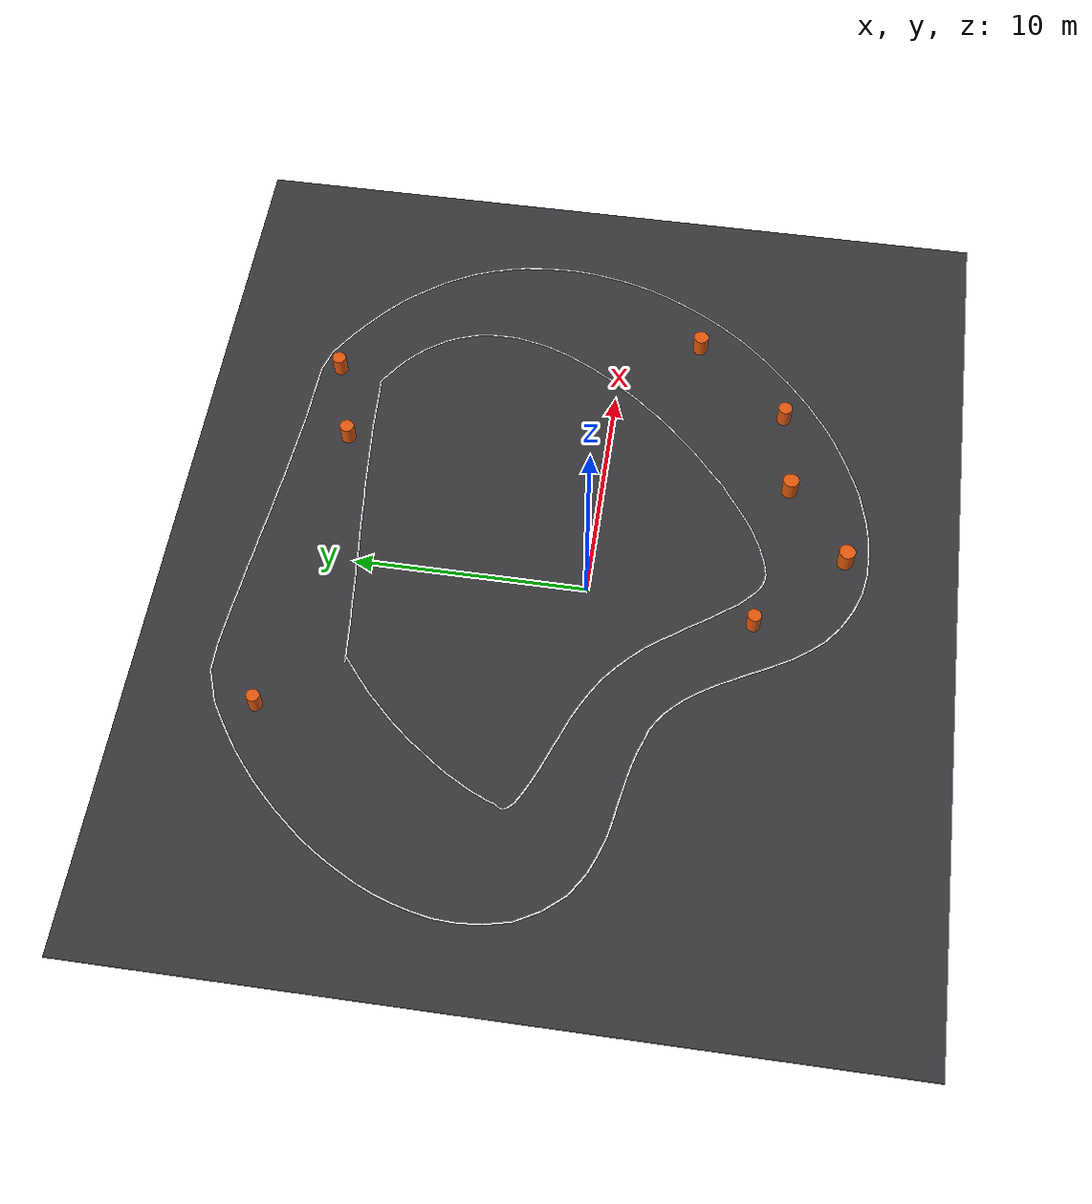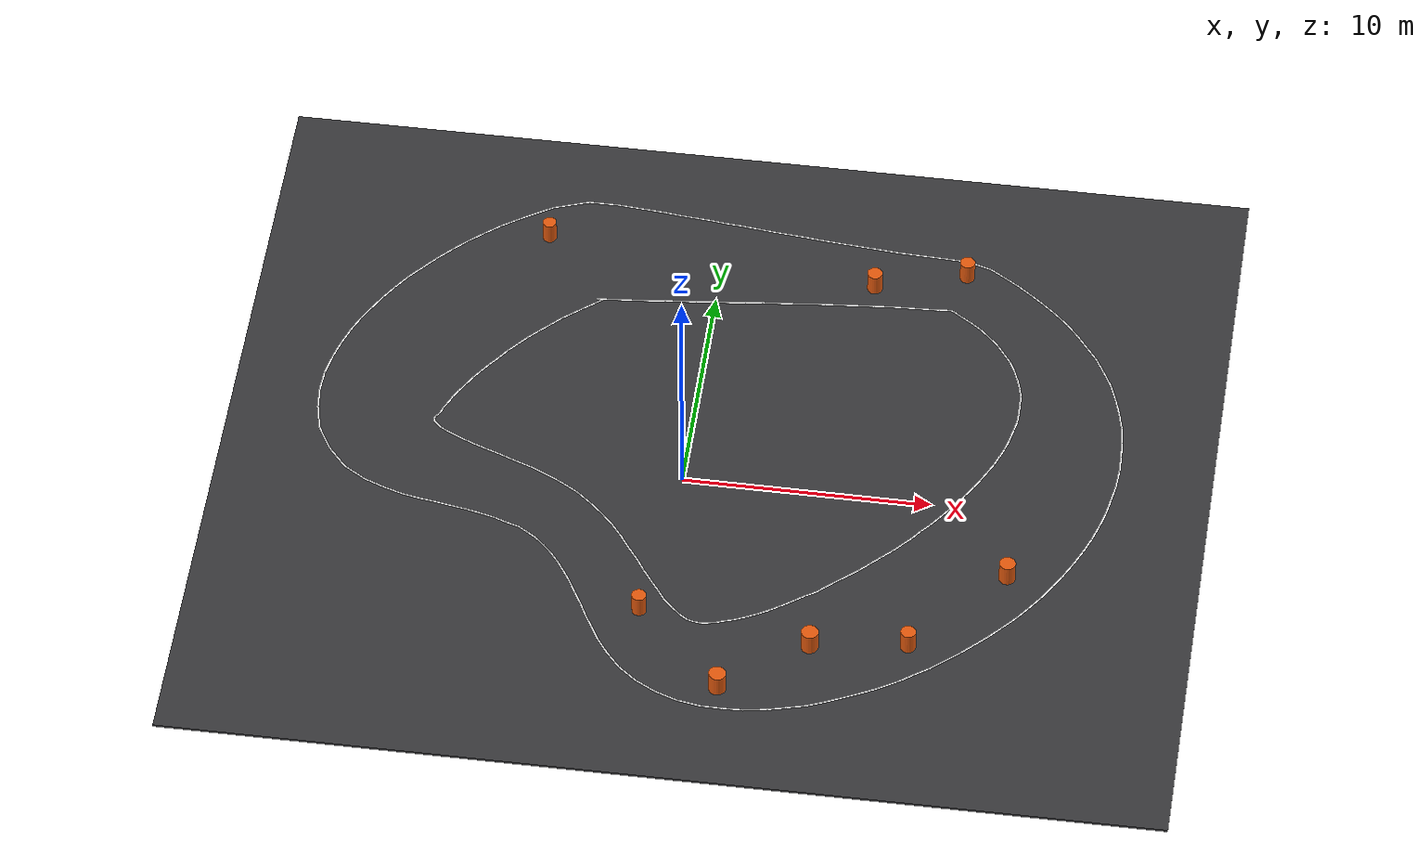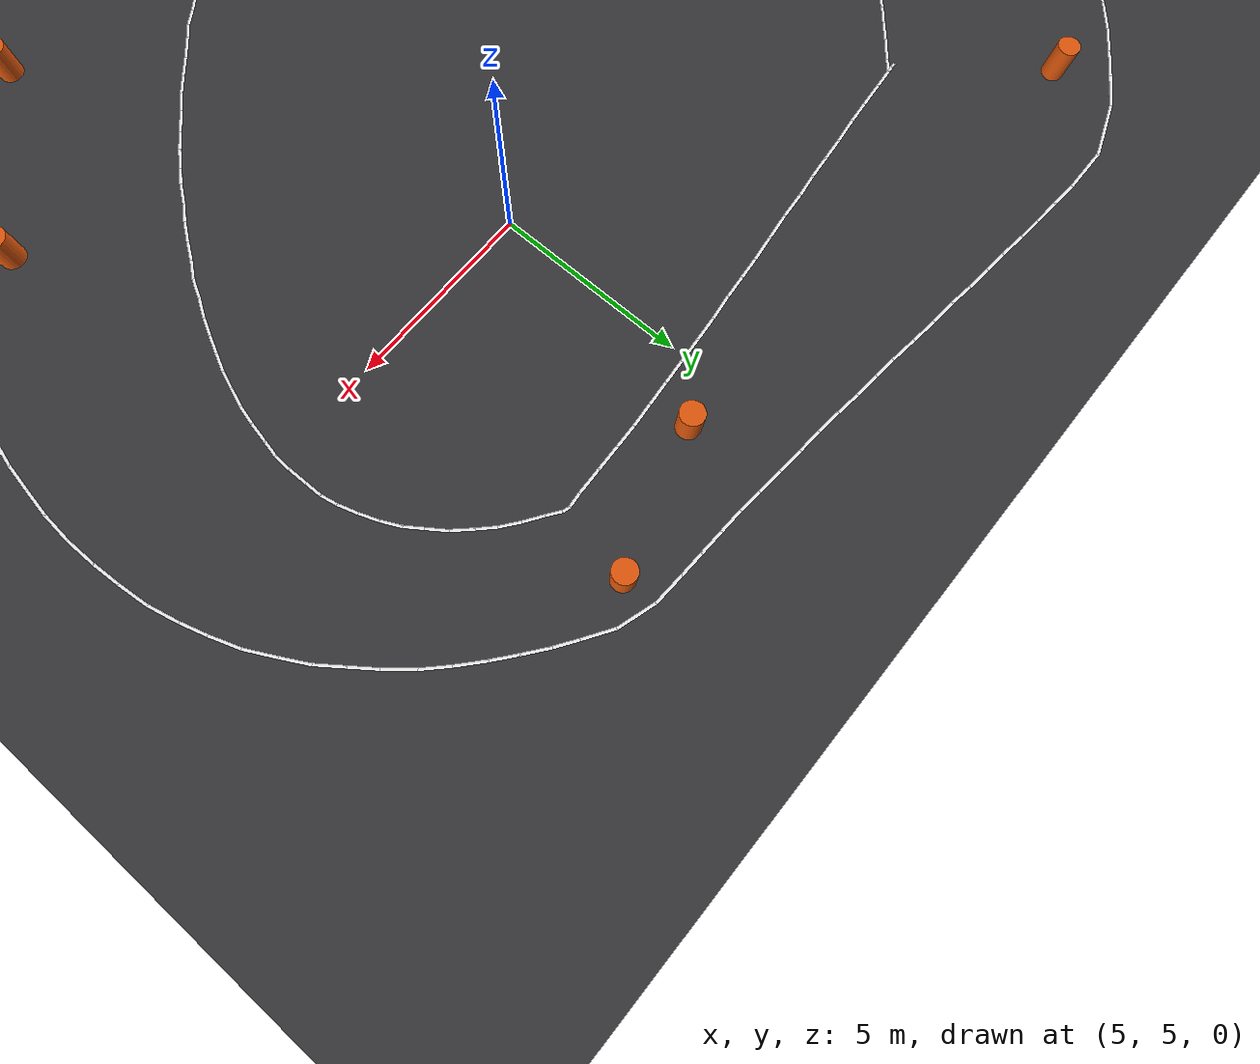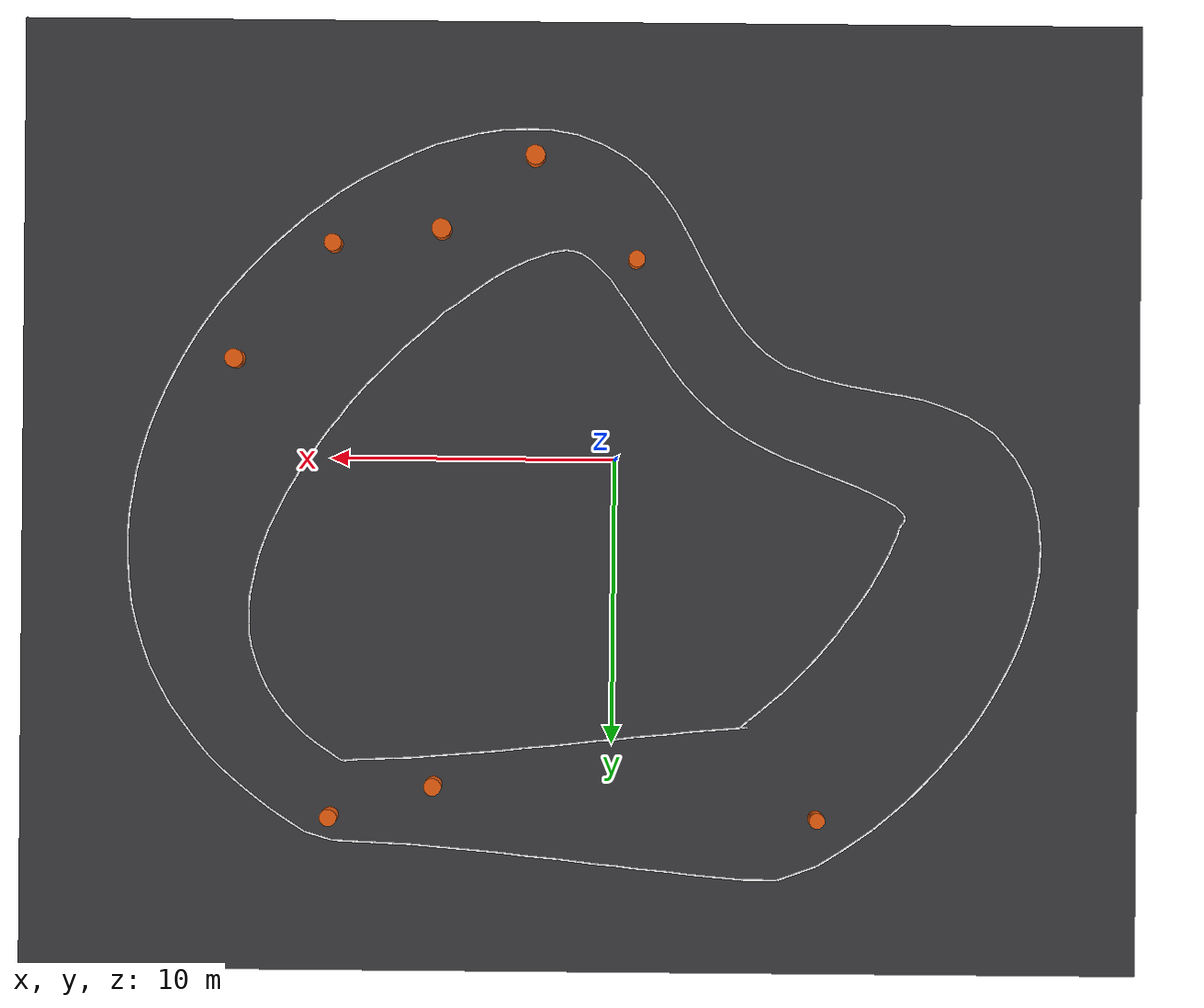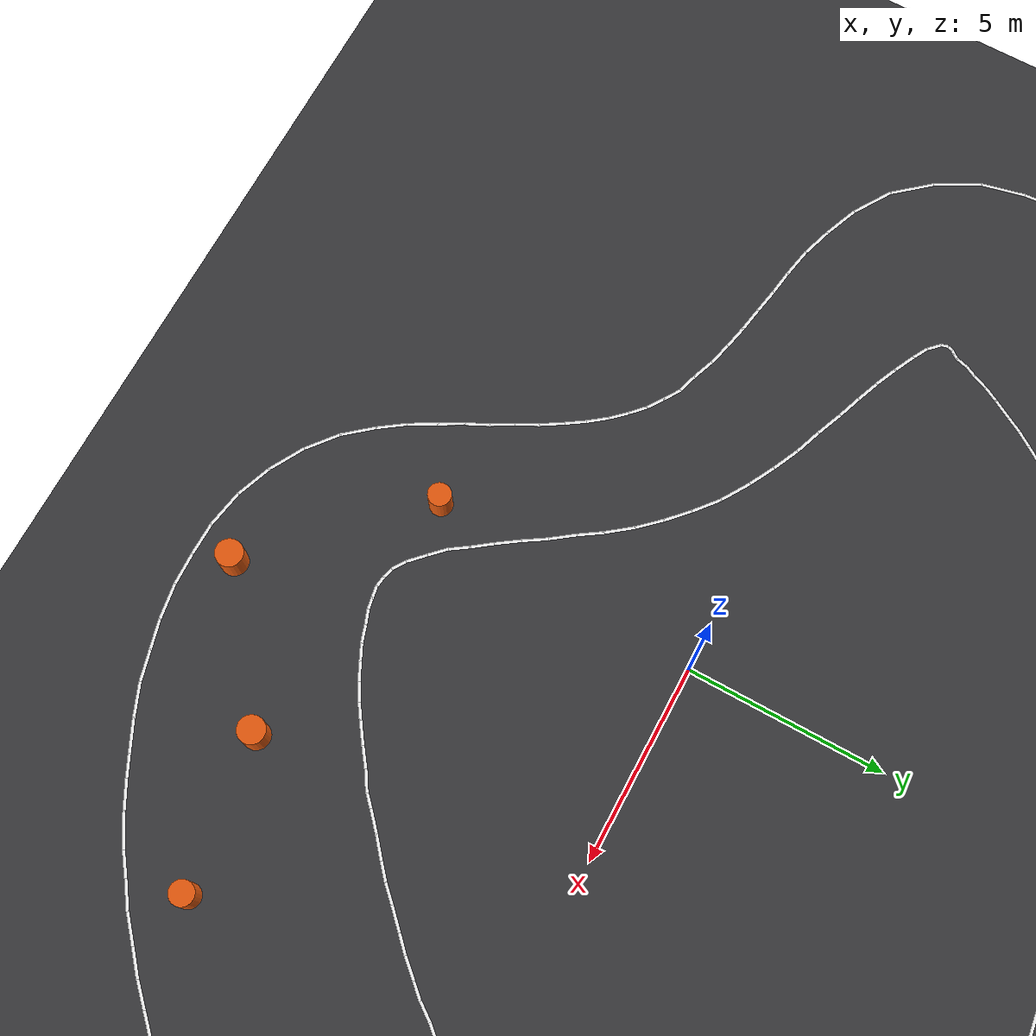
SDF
<?xml version="1.0" ?>
<sdf version="1.9">
  <world name="igvc_course">

    <physics name="1ms" type="ignored">
      <max_step_size>0.001</max_step_size>
      <real_time_factor>1.0</real_time_factor>
    </physics>

    <plugin filename="gz-sim-physics-system"
            name="gz::sim::systems::Physics"/>
    <plugin filename="gz-sim-user-commands-system"
            name="gz::sim::systems::UserCommands"/>
    <plugin filename="gz-sim-scene-broadcaster-system"
            name="gz::sim::systems::SceneBroadcaster"/>
    <plugin filename="gz-sim-sensors-system"
            name="gz::sim::systems::Sensors">
      <render_engine>ogre2</render_engine>
    </plugin>
    <plugin filename="gz-sim-imu-system"
            name="gz::sim::systems::Imu"/>

    <light type="directional" name="sun">
      <cast_shadows>true</cast_shadows>
      <pose>0 0 12 0 0 0</pose>
      <diffuse>0.9 0.9 0.9 1</diffuse>
      <specular>0.25 0.25 0.25 1</specular>
      <direction>-0.4 0.2 -0.9</direction>
    </light>

    <scene>
      <ambient>0.45 0.45 0.45 1</ambient>
      <background>0.55 0.68 0.85 1</background>
      <grid>false</grid>
    </scene>

    <!-- Asphalt. Deliberately dark so the white lane paint has contrast for
         the camera; lane detection is the reason this world exists. -->
    <model name="ground">
      <static>true</static>
      <pose>1.1853 1.2982 -0.05 0 0 0</pose>
      <link name="link">
        <collision name="collision">
          <geometry><box><size>39.54 33.62 0.1</size></box></geometry>
          <surface><friction><ode><mu>1.0</mu><mu2>1.0</mu2></ode></friction></surface>
        </collision>
        <visual name="visual">
          <geometry><box><size>39.54 33.62 0.1</size></box></geometry>
          <material>
            <ambient>0.18 0.18 0.19 1</ambient>
            <diffuse>0.22 0.22 0.23 1</diffuse>
          </material>
        </visual>
      </link>
    </model>

    <model name="lane_left_0">
      <static>true</static>
      <pose>-13.8306 -0.6216 0.0025 0 0 2.27805</pose>
      <link name="link">
        <visual name="visual">
          <geometry><box><size>1.2088 0.0762 0.0050</size></box></geometry>
          <material>
            <ambient>0.95 0.95 0.95 1</ambient>
            <diffuse>0.95 0.95 0.95 1</diffuse>
            <specular>0.1 0.1 0.1 1</specular>
            <emissive>0.55 0.55 0.55 1</emissive>
          </material>
        </visual>
      </link>
    </model>
    <model name="lane_left_1">
      <static>true</static>
      <pose>-14.5012 0.3467 0.0025 0 0 2.07716</pose>
      <link name="link">
        <visual name="visual">
          <geometry><box><size>1.2349 0.0762 0.0050</size></box></geometry>
          <material>
            <ambient>0.95 0.95 0.95 1</ambient>
            <diffuse>0.95 0.95 0.95 1</diffuse>
            <specular>0.1 0.1 0.1 1</specular>
            <emissive>0.55 0.55 0.55 1</emissive>
          </material>
        </visual>
      </link>
    </model>
    <model name="lane_left_2">
      <static>true</static>
      <pose>-14.9191 1.4255 0.0025 0 0 1.79683</pose>
      <link name="link">
        <visual name="visual">
          <geometry><box><size>1.1780 0.0762 0.0050</size></box></geometry>
          <material>
            <ambient>0.95 0.95 0.95 1</ambient>
            <diffuse>0.95 0.95 0.95 1</diffuse>
            <specular>0.1 0.1 0.1 1</specular>
            <emissive>0.55 0.55 0.55 1</emissive>
          </material>
        </visual>
      </link>
    </model>
    <model name="lane_left_3">
      <static>true</static>
      <pose>-15.0890 2.4742 0.0025 0 0 1.65596</pose>
      <link name="link">
        <visual name="visual">
          <geometry><box><size>1.0282 0.0762 0.0050</size></box></geometry>
          <material>
            <ambient>0.95 0.95 0.95 1</ambient>
            <diffuse>0.95 0.95 0.95 1</diffuse>
            <specular>0.1 0.1 0.1 1</specular>
            <emissive>0.55 0.55 0.55 1</emissive>
          </material>
        </visual>
      </link>
    </model>
    <model name="lane_left_4">
      <static>true</static>
      <pose>-15.1073 3.4410 0.0025 0 0 1.52065</pose>
      <link name="link">
        <visual name="visual">
          <geometry><box><size>0.9865 0.0762 0.0050</size></box></geometry>
          <material>
            <ambient>0.95 0.95 0.95 1</ambient>
            <diffuse>0.95 0.95 0.95 1</diffuse>
            <specular>0.1 0.1 0.1 1</specular>
            <emissive>0.55 0.55 0.55 1</emissive>
          </material>
        </visual>
      </link>
    </model>
    <model name="lane_left_5">
      <static>true</static>
      <pose>-14.9963 4.3646 0.0025 0 0 1.37917</pose>
      <link name="link">
        <visual name="visual">
          <geometry><box><size>0.9548 0.0762 0.0050</size></box></geometry>
          <material>
            <ambient>0.95 0.95 0.95 1</ambient>
            <diffuse>0.95 0.95 0.95 1</diffuse>
            <specular>0.1 0.1 0.1 1</specular>
            <emissive>0.55 0.55 0.55 1</emissive>
          </material>
        </visual>
      </link>
    </model>
    <model name="lane_left_6">
      <static>true</static>
      <pose>-14.8020 5.2068 0.0025 0 0 1.30455</pose>
      <link name="link">
        <visual name="visual">
          <geometry><box><size>0.8513 0.0762 0.0050</size></box></geometry>
          <material>
            <ambient>0.95 0.95 0.95 1</ambient>
            <diffuse>0.95 0.95 0.95 1</diffuse>
            <specular>0.1 0.1 0.1 1</specular>
            <emissive>0.55 0.55 0.55 1</emissive>
          </material>
        </visual>
      </link>
    </model>
    <model name="lane_left_7">
      <static>true</static>
      <pose>-14.5667 5.9713 0.0025 0 0 1.23896</pose>
      <link name="link">
        <visual name="visual">
          <geometry><box><size>0.8255 0.0762 0.0050</size></box></geometry>
          <material>
            <ambient>0.95 0.95 0.95 1</ambient>
            <diffuse>0.95 0.95 0.95 1</diffuse>
            <specular>0.1 0.1 0.1 1</specular>
            <emissive>0.55 0.55 0.55 1</emissive>
          </material>
        </visual>
      </link>
    </model>
    <model name="lane_left_8">
      <static>true</static>
      <pose>-14.2861 6.6958 0.0025 0 0 1.16262</pose>
      <link name="link">
        <visual name="visual">
          <geometry><box><size>0.8058 0.0762 0.0050</size></box></geometry>
          <material>
            <ambient>0.95 0.95 0.95 1</ambient>
            <diffuse>0.95 0.95 0.95 1</diffuse>
            <specular>0.1 0.1 0.1 1</specular>
            <emissive>0.55 0.55 0.55 1</emissive>
          </material>
        </visual>
      </link>
    </model>
    <model name="lane_left_9">
      <static>true</static>
      <pose>-13.9547 7.3877 0.0025 0 0 1.08552</pose>
      <link name="link">
        <visual name="visual">
          <geometry><box><size>0.8057 0.0762 0.0050</size></box></geometry>
          <material>
            <ambient>0.95 0.95 0.95 1</ambient>
            <diffuse>0.95 0.95 0.95 1</diffuse>
            <specular>0.1 0.1 0.1 1</specular>
            <emissive>0.55 0.55 0.55 1</emissive>
          </material>
        </visual>
      </link>
    </model>
    <model name="lane_left_10">
      <static>true</static>
      <pose>-13.6029 8.0362 0.0025 0 0 1.06093</pose>
      <link name="link">
        <visual name="visual">
          <geometry><box><size>0.7462 0.0762 0.0050</size></box></geometry>
          <material>
            <ambient>0.95 0.95 0.95 1</ambient>
            <diffuse>0.95 0.95 0.95 1</diffuse>
            <specular>0.1 0.1 0.1 1</specular>
            <emissive>0.55 0.55 0.55 1</emissive>
          </material>
        </visual>
      </link>
    </model>
    <model name="lane_left_11">
      <static>true</static>
      <pose>-13.2385 8.6509 0.0025 0 0 1.01109</pose>
      <link name="link">
        <visual name="visual">
          <geometry><box><size>0.7595 0.0762 0.0050</size></box></geometry>
          <material>
            <ambient>0.95 0.95 0.95 1</ambient>
            <diffuse>0.95 0.95 0.95 1</diffuse>
            <specular>0.1 0.1 0.1 1</specular>
            <emissive>0.55 0.55 0.55 1</emissive>
          </material>
        </visual>
      </link>
    </model>
    <model name="lane_left_12">
      <static>true</static>
      <pose>-12.8229 9.2812 0.0025 0 0 0.96653</pose>
      <link name="link">
        <visual name="visual">
          <geometry><box><size>0.8271 0.0762 0.0050</size></box></geometry>
          <material>
            <ambient>0.95 0.95 0.95 1</ambient>
            <diffuse>0.95 0.95 0.95 1</diffuse>
            <specular>0.1 0.1 0.1 1</specular>
            <emissive>0.55 0.55 0.55 1</emissive>
          </material>
        </visual>
      </link>
    </model>
    <model name="lane_left_13">
      <static>true</static>
      <pose>-12.3445 9.9135 0.0025 0 0 0.88008</pose>
      <link name="link">
        <visual name="visual">
          <geometry><box><size>0.8362 0.0762 0.0050</size></box></geometry>
          <material>
            <ambient>0.95 0.95 0.95 1</ambient>
            <diffuse>0.95 0.95 0.95 1</diffuse>
            <specular>0.1 0.1 0.1 1</specular>
            <emissive>0.55 0.55 0.55 1</emissive>
          </material>
        </visual>
      </link>
    </model>
    <model name="lane_left_14">
      <static>true</static>
      <pose>-11.8483 10.5103 0.0025 0 0 0.87409</pose>
      <link name="link">
        <visual name="visual">
          <geometry><box><size>0.7924 0.0762 0.0050</size></box></geometry>
          <material>
            <ambient>0.95 0.95 0.95 1</ambient>
            <diffuse>0.95 0.95 0.95 1</diffuse>
            <specular>0.1 0.1 0.1 1</specular>
            <emissive>0.55 0.55 0.55 1</emissive>
          </material>
        </visual>
      </link>
    </model>
    <model name="lane_left_15">
      <static>true</static>
      <pose>-11.3224 11.1009 0.0025 0 0 0.81522</pose>
      <link name="link">
        <visual name="visual">
          <geometry><box><size>0.8659 0.0762 0.0050</size></box></geometry>
          <material>
            <ambient>0.95 0.95 0.95 1</ambient>
            <diffuse>0.95 0.95 0.95 1</diffuse>
            <specular>0.1 0.1 0.1 1</specular>
            <emissive>0.55 0.55 0.55 1</emissive>
          </material>
        </visual>
      </link>
    </model>
    <model name="lane_left_16">
      <static>true</static>
      <pose>-10.7684 11.6724 0.0025 0 0 0.78537</pose>
      <link name="link">
        <visual name="visual">
          <geometry><box><size>0.8024 0.0762 0.0050</size></box></geometry>
          <material>
            <ambient>0.95 0.95 0.95 1</ambient>
            <diffuse>0.95 0.95 0.95 1</diffuse>
            <specular>0.1 0.1 0.1 1</specular>
            <emissive>0.55 0.55 0.55 1</emissive>
          </material>
        </visual>
      </link>
    </model>
    <model name="lane_left_17">
      <static>true</static>
      <pose>-10.2001 12.2030 0.0025 0 0 0.71821</pose>
      <link name="link">
        <visual name="visual">
          <geometry><box><size>0.8297 0.0762 0.0050</size></box></geometry>
          <material>
            <ambient>0.95 0.95 0.95 1</ambient>
            <diffuse>0.95 0.95 0.95 1</diffuse>
            <specular>0.1 0.1 0.1 1</specular>
            <emissive>0.55 0.55 0.55 1</emissive>
          </material>
        </visual>
      </link>
    </model>
    <model name="lane_left_18">
      <static>true</static>
      <pose>-9.5927 12.7217 0.0025 0 0 0.69565</pose>
      <link name="link">
        <visual name="visual">
          <geometry><box><size>0.8441 0.0762 0.0050</size></box></geometry>
          <material>
            <ambient>0.95 0.95 0.95 1</ambient>
            <diffuse>0.95 0.95 0.95 1</diffuse>
            <specular>0.1 0.1 0.1 1</specular>
            <emissive>0.55 0.55 0.55 1</emissive>
          </material>
        </visual>
      </link>
    </model>
    <model name="lane_left_19">
      <static>true</static>
      <pose>-8.9993 13.1798 0.0025 0 0 0.61302</pose>
      <link name="link">
        <visual name="visual">
          <geometry><box><size>0.7326 0.0762 0.0050</size></box></geometry>
          <material>
            <ambient>0.95 0.95 0.95 1</ambient>
            <diffuse>0.95 0.95 0.95 1</diffuse>
            <specular>0.1 0.1 0.1 1</specular>
            <emissive>0.55 0.55 0.55 1</emissive>
          </material>
        </visual>
      </link>
    </model>
    <model name="lane_left_20">
      <static>true</static>
      <pose>-8.4093 13.5874 0.0025 0 0 0.59643</pose>
      <link name="link">
        <visual name="visual">
          <geometry><box><size>0.7779 0.0762 0.0050</size></box></geometry>
          <material>
            <ambient>0.95 0.95 0.95 1</ambient>
            <diffuse>0.95 0.95 0.95 1</diffuse>
            <specular>0.1 0.1 0.1 1</specular>
            <emissive>0.55 0.55 0.55 1</emissive>
          </material>
        </visual>
      </link>
    </model>
    <model name="lane_left_21">
      <static>true</static>
      <pose>-7.7038 14.0453 0.0025 0 0 0.55947</pose>
      <link name="link">
        <visual name="visual">
          <geometry><box><size>0.9808 0.0762 0.0050</size></box></geometry>
          <material>
            <ambient>0.95 0.95 0.95 1</ambient>
            <diffuse>0.95 0.95 0.95 1</diffuse>
            <specular>0.1 0.1 0.1 1</specular>
            <emissive>0.55 0.55 0.55 1</emissive>
          </material>
        </visual>
      </link>
    </model>
    <model name="lane_left_22">
      <static>true</static>
      <pose>-6.6085 14.5472 0.0025 0 0 0.34724</pose>
      <link name="link">
        <visual name="visual">
          <geometry><box><size>1.5179 0.0762 0.0050</size></box></geometry>
          <material>
            <ambient>0.95 0.95 0.95 1</ambient>
            <diffuse>0.95 0.95 0.95 1</diffuse>
            <specular>0.1 0.1 0.1 1</specular>
            <emissive>0.55 0.55 0.55 1</emissive>
          </material>
        </visual>
      </link>
    </model>
    <model name="lane_left_23">
      <static>true</static>
      <pose>-5.2988 14.7987 0.0025 0 0 -0.00058</pose>
      <link name="link">
        <visual name="visual">
          <geometry><box><size>1.2660 0.0762 0.0050</size></box></geometry>
          <material>
            <ambient>0.95 0.95 0.95 1</ambient>
            <diffuse>0.95 0.95 0.95 1</diffuse>
            <specular>0.1 0.1 0.1 1</specular>
            <emissive>0.55 0.55 0.55 1</emissive>
          </material>
        </visual>
      </link>
    </model>
    <model name="lane_left_24">
      <static>true</static>
      <pose>-4.3603 14.7701 0.0025 0 0 -0.08674</pose>
      <link name="link">
        <visual name="visual">
          <geometry><box><size>0.6897 0.0762 0.0050</size></box></geometry>
          <material>
            <ambient>0.95 0.95 0.95 1</ambient>
            <diffuse>0.95 0.95 0.95 1</diffuse>
            <specular>0.1 0.1 0.1 1</specular>
            <emissive>0.55 0.55 0.55 1</emissive>
          </material>
        </visual>
      </link>
    </model>
    <model name="lane_left_25">
      <static>true</static>
      <pose>-3.6971 14.7137 0.0025 0 0 -0.08314</pose>
      <link name="link">
        <visual name="visual">
          <geometry><box><size>0.7178 0.0762 0.0050</size></box></geometry>
          <material>
            <ambient>0.95 0.95 0.95 1</ambient>
            <diffuse>0.95 0.95 0.95 1</diffuse>
            <specular>0.1 0.1 0.1 1</specular>
            <emissive>0.55 0.55 0.55 1</emissive>
          </material>
        </visual>
      </link>
    </model>
    <model name="lane_left_26">
      <static>true</static>
      <pose>-3.0480 14.6572 0.0025 0 0 -0.09066</pose>
      <link name="link">
        <visual name="visual">
          <geometry><box><size>0.6615 0.0762 0.0050</size></box></geometry>
          <material>
            <ambient>0.95 0.95 0.95 1</ambient>
            <diffuse>0.95 0.95 0.95 1</diffuse>
            <specular>0.1 0.1 0.1 1</specular>
            <emissive>0.55 0.55 0.55 1</emissive>
          </material>
        </visual>
      </link>
    </model>
    <model name="lane_left_27">
      <static>true</static>
      <pose>-2.3989 14.5867 0.0025 0 0 -0.12435</pose>
      <link name="link">
        <visual name="visual">
          <geometry><box><size>0.7207 0.0762 0.0050</size></box></geometry>
          <material>
            <ambient>0.95 0.95 0.95 1</ambient>
            <diffuse>0.95 0.95 0.95 1</diffuse>
            <specular>0.1 0.1 0.1 1</specular>
            <emissive>0.55 0.55 0.55 1</emissive>
          </material>
        </visual>
      </link>
    </model>
    <model name="lane_left_28">
      <static>true</static>
      <pose>-1.7498 14.5161 0.0025 0 0 -0.09066</pose>
      <link name="link">
        <visual name="visual">
          <geometry><box><size>0.6615 0.0762 0.0050</size></box></geometry>
          <material>
            <ambient>0.95 0.95 0.95 1</ambient>
            <diffuse>0.95 0.95 0.95 1</diffuse>
            <specular>0.1 0.1 0.1 1</specular>
            <emissive>0.55 0.55 0.55 1</emissive>
          </material>
        </visual>
      </link>
    </model>
    <model name="lane_left_29">
      <static>true</static>
      <pose>-1.1289 14.4597 0.0025 0 0 -0.09066</pose>
      <link name="link">
        <visual name="visual">
          <geometry><box><size>0.6615 0.0762 0.0050</size></box></geometry>
          <material>
            <ambient>0.95 0.95 0.95 1</ambient>
            <diffuse>0.95 0.95 0.95 1</diffuse>
            <specular>0.1 0.1 0.1 1</specular>
            <emissive>0.55 0.55 0.55 1</emissive>
          </material>
        </visual>
      </link>
    </model>
    <model name="lane_left_30">
      <static>true</static>
      <pose>-0.5080 14.3891 0.0025 0 0 -0.13553</pose>
      <link name="link">
        <visual name="visual">
          <geometry><box><size>0.6647 0.0762 0.0050</size></box></geometry>
          <material>
            <ambient>0.95 0.95 0.95 1</ambient>
            <diffuse>0.95 0.95 0.95 1</diffuse>
            <specular>0.1 0.1 0.1 1</specular>
            <emissive>0.55 0.55 0.55 1</emissive>
          </material>
        </visual>
      </link>
    </model>
    <model name="lane_left_31">
      <static>true</static>
      <pose>0.1552 14.3185 0.0025 0 0 -0.07983</pose>
      <link name="link">
        <visual name="visual">
          <geometry><box><size>0.7459 0.0762 0.0050</size></box></geometry>
          <material>
            <ambient>0.95 0.95 0.95 1</ambient>
            <diffuse>0.95 0.95 0.95 1</diffuse>
            <specular>0.1 0.1 0.1 1</specular>
            <emissive>0.55 0.55 0.55 1</emissive>
          </material>
        </visual>
      </link>
    </model>
    <model name="lane_left_32">
      <static>true</static>
      <pose>0.8608 14.2480 0.0025 0 0 -0.11943</pose>
      <link name="link">
        <visual name="visual">
          <geometry><box><size>0.7487 0.0762 0.0050</size></box></geometry>
          <material>
            <ambient>0.95 0.95 0.95 1</ambient>
            <diffuse>0.95 0.95 0.95 1</diffuse>
            <specular>0.1 0.1 0.1 1</specular>
            <emissive>0.55 0.55 0.55 1</emissive>
          </material>
        </visual>
      </link>
    </model>
    <model name="lane_left_33">
      <static>true</static>
      <pose>1.5522 14.1633 0.0025 0 0 -0.12435</pose>
      <link name="link">
        <visual name="visual">
          <geometry><box><size>0.7207 0.0762 0.0050</size></box></geometry>
          <material>
            <ambient>0.95 0.95 0.95 1</ambient>
            <diffuse>0.95 0.95 0.95 1</diffuse>
            <specular>0.1 0.1 0.1 1</specular>
            <emissive>0.55 0.55 0.55 1</emissive>
          </material>
        </visual>
      </link>
    </model>
    <model name="lane_left_34">
      <static>true</static>
      <pose>2.2013 14.0928 0.0025 0 0 -0.09066</pose>
      <link name="link">
        <visual name="visual">
          <geometry><box><size>0.6615 0.0762 0.0050</size></box></geometry>
          <material>
            <ambient>0.95 0.95 0.95 1</ambient>
            <diffuse>0.95 0.95 0.95 1</diffuse>
            <specular>0.1 0.1 0.1 1</specular>
            <emissive>0.55 0.55 0.55 1</emissive>
          </material>
        </visual>
      </link>
    </model>
    <model name="lane_left_35">
      <static>true</static>
      <pose>2.8222 14.0363 0.0025 0 0 -0.09066</pose>
      <link name="link">
        <visual name="visual">
          <geometry><box><size>0.6615 0.0762 0.0050</size></box></geometry>
          <material>
            <ambient>0.95 0.95 0.95 1</ambient>
            <diffuse>0.95 0.95 0.95 1</diffuse>
            <specular>0.1 0.1 0.1 1</specular>
            <emissive>0.55 0.55 0.55 1</emissive>
          </material>
        </visual>
      </link>
    </model>
    <model name="lane_left_36">
      <static>true</static>
      <pose>3.4713 13.9658 0.0025 0 0 -0.12435</pose>
      <link name="link">
        <visual name="visual">
          <geometry><box><size>0.7207 0.0762 0.0050</size></box></geometry>
          <material>
            <ambient>0.95 0.95 0.95 1</ambient>
            <diffuse>0.95 0.95 0.95 1</diffuse>
            <specular>0.1 0.1 0.1 1</specular>
            <emissive>0.55 0.55 0.55 1</emissive>
          </material>
        </visual>
      </link>
    </model>
    <model name="lane_left_37">
      <static>true</static>
      <pose>4.1204 13.8952 0.0025 0 0 -0.09066</pose>
      <link name="link">
        <visual name="visual">
          <geometry><box><size>0.6615 0.0762 0.0050</size></box></geometry>
          <material>
            <ambient>0.95 0.95 0.95 1</ambient>
            <diffuse>0.95 0.95 0.95 1</diffuse>
            <specular>0.1 0.1 0.1 1</specular>
            <emissive>0.55 0.55 0.55 1</emissive>
          </material>
        </visual>
      </link>
    </model>
    <model name="lane_left_38">
      <static>true</static>
      <pose>4.7696 13.8388 0.0025 0 0 -0.08314</pose>
      <link name="link">
        <visual name="visual">
          <geometry><box><size>0.7178 0.0762 0.0050</size></box></geometry>
          <material>
            <ambient>0.95 0.95 0.95 1</ambient>
            <diffuse>0.95 0.95 0.95 1</diffuse>
            <specular>0.1 0.1 0.1 1</specular>
            <emissive>0.55 0.55 0.55 1</emissive>
          </material>
        </visual>
      </link>
    </model>
    <model name="lane_left_39">
      <static>true</static>
      <pose>5.4328 13.7823 0.0025 0 0 -0.08674</pose>
      <link name="link">
        <visual name="visual">
          <geometry><box><size>0.6897 0.0762 0.0050</size></box></geometry>
          <material>
            <ambient>0.95 0.95 0.95 1</ambient>
            <diffuse>0.95 0.95 0.95 1</diffuse>
            <specular>0.1 0.1 0.1 1</specular>
            <emissive>0.55 0.55 0.55 1</emissive>
          </material>
        </visual>
      </link>
    </model>
    <model name="lane_left_40">
      <static>true</static>
      <pose>6.0960 13.7259 0.0025 0 0 -0.08314</pose>
      <link name="link">
        <visual name="visual">
          <geometry><box><size>0.7178 0.0762 0.0050</size></box></geometry>
          <material>
            <ambient>0.95 0.95 0.95 1</ambient>
            <diffuse>0.95 0.95 0.95 1</diffuse>
            <specular>0.1 0.1 0.1 1</specular>
            <emissive>0.55 0.55 0.55 1</emissive>
          </material>
        </visual>
      </link>
    </model>
    <model name="lane_left_41">
      <static>true</static>
      <pose>6.7451 13.6694 0.0025 0 0 -0.09066</pose>
      <link name="link">
        <visual name="visual">
          <geometry><box><size>0.6615 0.0762 0.0050</size></box></geometry>
          <material>
            <ambient>0.95 0.95 0.95 1</ambient>
            <diffuse>0.95 0.95 0.95 1</diffuse>
            <specular>0.1 0.1 0.1 1</specular>
            <emissive>0.55 0.55 0.55 1</emissive>
          </material>
        </visual>
      </link>
    </model>
    <model name="lane_left_42">
      <static>true</static>
      <pose>7.3801 13.6271 0.0025 0 0 -0.04345</pose>
      <link name="link">
        <visual name="visual">
          <geometry><box><size>0.6878 0.0762 0.0050</size></box></geometry>
          <material>
            <ambient>0.95 0.95 0.95 1</ambient>
            <diffuse>0.95 0.95 0.95 1</diffuse>
            <specular>0.1 0.1 0.1 1</specular>
            <emissive>0.55 0.55 0.55 1</emissive>
          </material>
        </visual>
      </link>
    </model>
    <model name="lane_left_43">
      <static>true</static>
      <pose>8.0433 13.5989 0.0025 0 0 -0.04164</pose>
      <link name="link">
        <visual name="visual">
          <geometry><box><size>0.7160 0.0762 0.0050</size></box></geometry>
          <material>
            <ambient>0.95 0.95 0.95 1</ambient>
            <diffuse>0.95 0.95 0.95 1</diffuse>
            <specular>0.1 0.1 0.1 1</specular>
            <emissive>0.55 0.55 0.55 1</emissive>
          </material>
        </visual>
      </link>
    </model>
    <model name="lane_left_44">
      <static>true</static>
      <pose>8.7207 13.5707 0.0025 0 0 -0.04164</pose>
      <link name="link">
        <visual name="visual">
          <geometry><box><size>0.7160 0.0762 0.0050</size></box></geometry>
          <material>
            <ambient>0.95 0.95 0.95 1</ambient>
            <diffuse>0.95 0.95 0.95 1</diffuse>
            <specular>0.1 0.1 0.1 1</specular>
            <emissive>0.55 0.55 0.55 1</emissive>
          </material>
        </visual>
      </link>
    </model>
    <model name="lane_left_45">
      <static>true</static>
      <pose>9.4703 13.5353 0.0025 0 0 -0.05167</pose>
      <link name="link">
        <visual name="visual">
          <geometry><box><size>0.8610 0.0762 0.0050</size></box></geometry>
          <material>
            <ambient>0.95 0.95 0.95 1</ambient>
            <diffuse>0.95 0.95 0.95 1</diffuse>
            <specular>0.1 0.1 0.1 1</specular>
            <emissive>0.55 0.55 0.55 1</emissive>
          </material>
        </visual>
      </link>
    </model>
    <model name="lane_left_46">
      <static>true</static>
      <pose>10.3671 13.3681 0.0025 0 0 -0.29174</pose>
      <link name="link">
        <visual name="visual">
          <geometry><box><size>1.0528 0.0762 0.0050</size></box></geometry>
          <material>
            <ambient>0.95 0.95 0.95 1</ambient>
            <diffuse>0.95 0.95 0.95 1</diffuse>
            <specular>0.1 0.1 0.1 1</specular>
            <emissive>0.55 0.55 0.55 1</emissive>
          </material>
        </visual>
      </link>
    </model>
    <model name="lane_left_47">
      <static>true</static>
      <pose>11.1969 13.0019 0.0025 0 0 -0.56959</pose>
      <link name="link">
        <visual name="visual">
          <geometry><box><size>0.8550 0.0762 0.0050</size></box></geometry>
          <material>
            <ambient>0.95 0.95 0.95 1</ambient>
            <diffuse>0.95 0.95 0.95 1</diffuse>
            <specular>0.1 0.1 0.1 1</specular>
            <emissive>0.55 0.55 0.55 1</emissive>
          </material>
        </visual>
      </link>
    </model>
    <model name="lane_left_48">
      <static>true</static>
      <pose>11.8137 12.5993 0.0025 0 0 -0.58913</pose>
      <link name="link">
        <visual name="visual">
          <geometry><box><size>0.6945 0.0762 0.0050</size></box></geometry>
          <material>
            <ambient>0.95 0.95 0.95 1</ambient>
            <diffuse>0.95 0.95 0.95 1</diffuse>
            <specular>0.1 0.1 0.1 1</specular>
            <emissive>0.55 0.55 0.55 1</emissive>
          </material>
        </visual>
      </link>
    </model>
    <model name="lane_left_49">
      <static>true</static>
      <pose>12.3634 12.2053 0.0025 0 0 -0.65287</pose>
      <link name="link">
        <visual name="visual">
          <geometry><box><size>0.7351 0.0762 0.0050</size></box></geometry>
          <material>
            <ambient>0.95 0.95 0.95 1</ambient>
            <diffuse>0.95 0.95 0.95 1</diffuse>
            <specular>0.1 0.1 0.1 1</specular>
            <emissive>0.55 0.55 0.55 1</emissive>
          </material>
        </visual>
      </link>
    </model>
    <model name="lane_left_50">
      <static>true</static>
      <pose>12.9036 11.7823 0.0025 0 0 -0.67625</pose>
      <link name="link">
        <visual name="visual">
          <geometry><box><size>0.7133 0.0762 0.0050</size></box></geometry>
          <material>
            <ambient>0.95 0.95 0.95 1</ambient>
            <diffuse>0.95 0.95 0.95 1</diffuse>
            <specular>0.1 0.1 0.1 1</specular>
            <emissive>0.55 0.55 0.55 1</emissive>
          </material>
        </visual>
      </link>
    </model>
    <model name="lane_left_51">
      <static>true</static>
      <pose>13.4496 11.3233 0.0025 0 0 -0.71932</pose>
      <link name="link">
        <visual name="visual">
          <geometry><box><size>0.7900 0.0762 0.0050</size></box></geometry>
          <material>
            <ambient>0.95 0.95 0.95 1</ambient>
            <diffuse>0.95 0.95 0.95 1</diffuse>
            <specular>0.1 0.1 0.1 1</specular>
            <emissive>0.55 0.55 0.55 1</emissive>
          </material>
        </visual>
      </link>
    </model>
    <model name="lane_left_52">
      <static>true</static>
      <pose>14.0043 10.8108 0.0025 0 0 -0.77221</pose>
      <link name="link">
        <visual name="visual">
          <geometry><box><size>0.7972 0.0762 0.0050</size></box></geometry>
          <material>
            <ambient>0.95 0.95 0.95 1</ambient>
            <diffuse>0.95 0.95 0.95 1</diffuse>
            <specular>0.1 0.1 0.1 1</specular>
            <emissive>0.55 0.55 0.55 1</emissive>
          </material>
        </visual>
      </link>
    </model>
    <model name="lane_left_53">
      <static>true</static>
      <pose>14.5223 10.2517 0.0025 0 0 -0.87440</pose>
      <link name="link">
        <visual name="visual">
          <geometry><box><size>0.8052 0.0762 0.0050</size></box></geometry>
          <material>
            <ambient>0.95 0.95 0.95 1</ambient>
            <diffuse>0.95 0.95 0.95 1</diffuse>
            <specular>0.1 0.1 0.1 1</specular>
            <emissive>0.55 0.55 0.55 1</emissive>
          </material>
        </visual>
      </link>
    </model>
    <model name="lane_left_54">
      <static>true</static>
      <pose>14.9909 9.6593 0.0025 0 0 -0.92940</pose>
      <link name="link">
        <visual name="visual">
          <geometry><box><size>0.7822 0.0762 0.0050</size></box></geometry>
          <material>
            <ambient>0.95 0.95 0.95 1</ambient>
            <diffuse>0.95 0.95 0.95 1</diffuse>
            <specular>0.1 0.1 0.1 1</specular>
            <emissive>0.55 0.55 0.55 1</emissive>
          </material>
        </visual>
      </link>
    </model>
    <model name="lane_left_55">
      <static>true</static>
      <pose>15.4342 9.0626 0.0025 0 0 -0.93430</pose>
      <link name="link">
        <visual name="visual">
          <geometry><box><size>0.7806 0.0762 0.0050</size></box></geometry>
          <material>
            <ambient>0.95 0.95 0.95 1</ambient>
            <diffuse>0.95 0.95 0.95 1</diffuse>
            <specular>0.1 0.1 0.1 1</specular>
            <emissive>0.55 0.55 0.55 1</emissive>
          </material>
        </visual>
      </link>
    </model>
    <model name="lane_left_56">
      <static>true</static>
      <pose>15.8338 8.4374 0.0025 0 0 -1.06964</pose>
      <link name="link">
        <visual name="visual">
          <geometry><box><size>0.7831 0.0762 0.0050</size></box></geometry>
          <material>
            <ambient>0.95 0.95 0.95 1</ambient>
            <diffuse>0.95 0.95 0.95 1</diffuse>
            <specular>0.1 0.1 0.1 1</specular>
            <emissive>0.55 0.55 0.55 1</emissive>
          </material>
        </visual>
      </link>
    </model>
    <model name="lane_left_57">
      <static>true</static>
      <pose>16.1950 7.7631 0.0025 0 0 -1.08808</pose>
      <link name="link">
        <visual name="visual">
          <geometry><box><size>0.8231 0.0762 0.0050</size></box></geometry>
          <material>
            <ambient>0.95 0.95 0.95 1</ambient>
            <diffuse>0.95 0.95 0.95 1</diffuse>
            <specular>0.1 0.1 0.1 1</specular>
            <emissive>0.55 0.55 0.55 1</emissive>
          </material>
        </visual>
      </link>
    </model>
    <model name="lane_left_58">
      <static>true</static>
      <pose>16.5127 7.0380 0.0025 0 0 -1.22600</pose>
      <link name="link">
        <visual name="visual">
          <geometry><box><size>0.8402 0.0762 0.0050</size></box></geometry>
          <material>
            <ambient>0.95 0.95 0.95 1</ambient>
            <diffuse>0.95 0.95 0.95 1</diffuse>
            <specular>0.1 0.1 0.1 1</specular>
            <emissive>0.55 0.55 0.55 1</emissive>
          </material>
        </visual>
      </link>
    </model>
    <model name="lane_left_59">
      <static>true</static>
      <pose>16.7550 6.3107 0.0025 0 0 -1.27469</pose>
      <link name="link">
        <visual name="visual">
          <geometry><box><size>0.7696 0.0762 0.0050</size></box></geometry>
          <material>
            <ambient>0.95 0.95 0.95 1</ambient>
            <diffuse>0.95 0.95 0.95 1</diffuse>
            <specular>0.1 0.1 0.1 1</specular>
            <emissive>0.55 0.55 0.55 1</emissive>
          </material>
        </visual>
      </link>
    </model>
    <model name="lane_left_60">
      <static>true</static>
      <pose>16.9565 5.5636 0.0025 0 0 -1.33669</pose>
      <link name="link">
        <visual name="visual">
          <geometry><box><size>0.8549 0.0762 0.0050</size></box></geometry>
          <material>
            <ambient>0.95 0.95 0.95 1</ambient>
            <diffuse>0.95 0.95 0.95 1</diffuse>
            <specular>0.1 0.1 0.1 1</specular>
            <emissive>0.55 0.55 0.55 1</emissive>
          </material>
        </visual>
      </link>
    </model>
    <model name="lane_left_61">
      <static>true</static>
      <pose>17.0957 4.7602 0.0025 0 0 -1.46166</pose>
      <link name="link">
        <visual name="visual">
          <geometry><box><size>0.8551 0.0762 0.0050</size></box></geometry>
          <material>
            <ambient>0.95 0.95 0.95 1</ambient>
            <diffuse>0.95 0.95 0.95 1</diffuse>
            <specular>0.1 0.1 0.1 1</specular>
            <emissive>0.55 0.55 0.55 1</emissive>
          </material>
        </visual>
      </link>
    </model>
    <model name="lane_left_62">
      <static>true</static>
      <pose>17.1663 3.9801 0.0025 0 0 -1.50117</pose>
      <link name="link">
        <visual name="visual">
          <geometry><box><size>0.7881 0.0762 0.0050</size></box></geometry>
          <material>
            <ambient>0.95 0.95 0.95 1</ambient>
            <diffuse>0.95 0.95 0.95 1</diffuse>
            <specular>0.1 0.1 0.1 1</specular>
            <emissive>0.55 0.55 0.55 1</emissive>
          </material>
        </visual>
      </link>
    </model>
    <model name="lane_left_63">
      <static>true</static>
      <pose>17.1990 3.2031 0.0025 0 0 -1.55433</pose>
      <link name="link">
        <visual name="visual">
          <geometry><box><size>0.8440 0.0762 0.0050</size></box></geometry>
          <material>
            <ambient>0.95 0.95 0.95 1</ambient>
            <diffuse>0.95 0.95 0.95 1</diffuse>
            <specular>0.1 0.1 0.1 1</specular>
            <emissive>0.55 0.55 0.55 1</emissive>
          </material>
        </visual>
      </link>
    </model>
    <model name="lane_left_64">
      <static>true</static>
      <pose>17.1767 2.3836 0.0025 0 0 -1.64017</pose>
      <link name="link">
        <visual name="visual">
          <geometry><box><size>0.8733 0.0762 0.0050</size></box></geometry>
          <material>
            <ambient>0.95 0.95 0.95 1</ambient>
            <diffuse>0.95 0.95 0.95 1</diffuse>
            <specular>0.1 0.1 0.1 1</specular>
            <emissive>0.55 0.55 0.55 1</emissive>
          </material>
        </visual>
      </link>
    </model>
    <model name="lane_left_65">
      <static>true</static>
      <pose>17.0895 1.5990 0.0025 0 0 -1.72789</pose>
      <link name="link">
        <visual name="visual">
          <geometry><box><size>0.7833 0.0762 0.0050</size></box></geometry>
          <material>
            <ambient>0.95 0.95 0.95 1</ambient>
            <diffuse>0.95 0.95 0.95 1</diffuse>
            <specular>0.1 0.1 0.1 1</specular>
            <emissive>0.55 0.55 0.55 1</emissive>
          </material>
        </visual>
      </link>
    </model>
    <model name="lane_left_66">
      <static>true</static>
      <pose>16.9692 0.8609 0.0025 0 0 -1.73664</pose>
      <link name="link">
        <visual name="visual">
          <geometry><box><size>0.7885 0.0762 0.0050</size></box></geometry>
          <material>
            <ambient>0.95 0.95 0.95 1</ambient>
            <diffuse>0.95 0.95 0.95 1</diffuse>
            <specular>0.1 0.1 0.1 1</specular>
            <emissive>0.55 0.55 0.55 1</emissive>
          </material>
        </visual>
      </link>
    </model>
    <model name="lane_left_67">
      <static>true</static>
      <pose>16.8168 0.1456 0.0025 0 0 -1.82708</pose>
      <link name="link">
        <visual name="visual">
          <geometry><box><size>0.7518 0.0762 0.0050</size></box></geometry>
          <material>
            <ambient>0.95 0.95 0.95 1</ambient>
            <diffuse>0.95 0.95 0.95 1</diffuse>
            <specular>0.1 0.1 0.1 1</specular>
            <emissive>0.55 0.55 0.55 1</emissive>
          </material>
        </visual>
      </link>
    </model>
    <model name="lane_left_68">
      <static>true</static>
      <pose>16.6131 -0.5734 0.0025 0 0 -1.86504</pose>
      <link name="link">
        <visual name="visual">
          <geometry><box><size>0.8192 0.0762 0.0050</size></box></geometry>
          <material>
            <ambient>0.95 0.95 0.95 1</ambient>
            <diffuse>0.95 0.95 0.95 1</diffuse>
            <specular>0.1 0.1 0.1 1</specular>
            <emissive>0.55 0.55 0.55 1</emissive>
          </material>
        </visual>
      </link>
    </model>
    <model name="lane_left_69">
      <static>true</static>
      <pose>16.3623 -1.3041 0.0025 0 0 -1.93861</pose>
      <link name="link">
        <visual name="visual">
          <geometry><box><size>0.8031 0.0762 0.0050</size></box></geometry>
          <material>
            <ambient>0.95 0.95 0.95 1</ambient>
            <diffuse>0.95 0.95 0.95 1</diffuse>
            <specular>0.1 0.1 0.1 1</specular>
            <emissive>0.55 0.55 0.55 1</emissive>
          </material>
        </visual>
      </link>
    </model>
    <model name="lane_left_70">
      <static>true</static>
      <pose>16.0663 -2.0229 0.0025 0 0 -1.98355</pose>
      <link name="link">
        <visual name="visual">
          <geometry><box><size>0.8283 0.0762 0.0050</size></box></geometry>
          <material>
            <ambient>0.95 0.95 0.95 1</ambient>
            <diffuse>0.95 0.95 0.95 1</diffuse>
            <specular>0.1 0.1 0.1 1</specular>
            <emissive>0.55 0.55 0.55 1</emissive>
          </material>
        </visual>
      </link>
    </model>
    <model name="lane_left_71">
      <static>true</static>
      <pose>15.7270 -2.7441 0.0025 0 0 -2.03704</pose>
      <link name="link">
        <visual name="visual">
          <geometry><box><size>0.8425 0.0762 0.0050</size></box></geometry>
          <material>
            <ambient>0.95 0.95 0.95 1</ambient>
            <diffuse>0.95 0.95 0.95 1</diffuse>
            <specular>0.1 0.1 0.1 1</specular>
            <emissive>0.55 0.55 0.55 1</emissive>
          </material>
        </visual>
      </link>
    </model>
    <model name="lane_left_72">
      <static>true</static>
      <pose>15.3887 -3.3878 0.0025 0 0 -2.07637</pose>
      <link name="link">
        <visual name="visual">
          <geometry><box><size>0.6884 0.0762 0.0050</size></box></geometry>
          <material>
            <ambient>0.95 0.95 0.95 1</ambient>
            <diffuse>0.95 0.95 0.95 1</diffuse>
            <specular>0.1 0.1 0.1 1</specular>
            <emissive>0.55 0.55 0.55 1</emissive>
          </material>
        </visual>
      </link>
    </model>
    <model name="lane_left_73">
      <static>true</static>
      <pose>15.0203 -4.0212 0.0025 0 0 -2.11457</pose>
      <link name="link">
        <visual name="visual">
          <geometry><box><size>0.8535 0.0762 0.0050</size></box></geometry>
          <material>
            <ambient>0.95 0.95 0.95 1</ambient>
            <diffuse>0.95 0.95 0.95 1</diffuse>
            <specular>0.1 0.1 0.1 1</specular>
            <emissive>0.55 0.55 0.55 1</emissive>
          </material>
        </visual>
      </link>
    </model>
    <model name="lane_left_74">
      <static>true</static>
      <pose>14.6150 -4.6493 0.0025 0 0 -2.17912</pose>
      <link name="link">
        <visual name="visual">
          <geometry><box><size>0.7185 0.0762 0.0050</size></box></geometry>
          <material>
            <ambient>0.95 0.95 0.95 1</ambient>
            <diffuse>0.95 0.95 0.95 1</diffuse>
            <specular>0.1 0.1 0.1 1</specular>
            <emissive>0.55 0.55 0.55 1</emissive>
          </material>
        </visual>
      </link>
    </model>
    <model name="lane_left_75">
      <static>true</static>
      <pose>14.2085 -5.2197 0.0025 0 0 -2.20013</pose>
      <link name="link">
        <visual name="visual">
          <geometry><box><size>0.7587 0.0762 0.0050</size></box></geometry>
          <material>
            <ambient>0.95 0.95 0.95 1</ambient>
            <diffuse>0.95 0.95 0.95 1</diffuse>
            <specular>0.1 0.1 0.1 1</specular>
            <emissive>0.55 0.55 0.55 1</emissive>
          </material>
        </visual>
      </link>
    </model>
    <model name="lane_left_76">
      <static>true</static>
      <pose>13.7522 -5.7925 0.0025 0 0 -2.28519</pose>
      <link name="link">
        <visual name="visual">
          <geometry><box><size>0.7834 0.0762 0.0050</size></box></geometry>
          <material>
            <ambient>0.95 0.95 0.95 1</ambient>
            <diffuse>0.95 0.95 0.95 1</diffuse>
            <specular>0.1 0.1 0.1 1</specular>
            <emissive>0.55 0.55 0.55 1</emissive>
          </material>
        </visual>
      </link>
    </model>
    <model name="lane_left_77">
      <static>true</static>
      <pose>13.2639 -6.3498 0.0025 0 0 -2.29569</pose>
      <link name="link">
        <visual name="visual">
          <geometry><box><size>0.7747 0.0762 0.0050</size></box></geometry>
          <material>
            <ambient>0.95 0.95 0.95 1</ambient>
            <diffuse>0.95 0.95 0.95 1</diffuse>
            <specular>0.1 0.1 0.1 1</specular>
            <emissive>0.55 0.55 0.55 1</emissive>
          </material>
        </visual>
      </link>
    </model>
    <model name="lane_left_78">
      <static>true</static>
      <pose>12.7622 -6.8840 0.0025 0 0 -2.35424</pose>
      <link name="link">
        <visual name="visual">
          <geometry><box><size>0.7678 0.0762 0.0050</size></box></geometry>
          <material>
            <ambient>0.95 0.95 0.95 1</ambient>
            <diffuse>0.95 0.95 0.95 1</diffuse>
            <specular>0.1 0.1 0.1 1</specular>
            <emissive>0.55 0.55 0.55 1</emissive>
          </material>
        </visual>
      </link>
    </model>
    <model name="lane_left_79">
      <static>true</static>
      <pose>12.2624 -7.3845 0.0025 0 0 -2.35673</pose>
      <link name="link">
        <visual name="visual">
          <geometry><box><size>0.7230 0.0762 0.0050</size></box></geometry>
          <material>
            <ambient>0.95 0.95 0.95 1</ambient>
            <diffuse>0.95 0.95 0.95 1</diffuse>
            <specular>0.1 0.1 0.1 1</specular>
            <emissive>0.55 0.55 0.55 1</emissive>
          </material>
        </visual>
      </link>
    </model>
    <model name="lane_left_80">
      <static>true</static>
      <pose>11.7511 -7.8594 0.0025 0 0 -2.42804</pose>
      <link name="link">
        <visual name="visual">
          <geometry><box><size>0.7497 0.0762 0.0050</size></box></geometry>
          <material>
            <ambient>0.95 0.95 0.95 1</ambient>
            <diffuse>0.95 0.95 0.95 1</diffuse>
            <specular>0.1 0.1 0.1 1</specular>
            <emissive>0.55 0.55 0.55 1</emissive>
          </material>
        </visual>
      </link>
    </model>
    <model name="lane_left_81">
      <static>true</static>
      <pose>11.1922 -8.3474 0.0025 0 0 -2.42001</pose>
      <link name="link">
        <visual name="visual">
          <geometry><box><size>0.8105 0.0762 0.0050</size></box></geometry>
          <material>
            <ambient>0.95 0.95 0.95 1</ambient>
            <diffuse>0.95 0.95 0.95 1</diffuse>
            <specular>0.1 0.1 0.1 1</specular>
            <emissive>0.55 0.55 0.55 1</emissive>
          </material>
        </visual>
      </link>
    </model>
    <model name="lane_left_82">
      <static>true</static>
      <pose>10.6202 -8.8047 0.0025 0 0 -2.51962</pose>
      <link name="link">
        <visual name="visual">
          <geometry><box><size>0.7322 0.0762 0.0050</size></box></geometry>
          <material>
            <ambient>0.95 0.95 0.95 1</ambient>
            <diffuse>0.95 0.95 0.95 1</diffuse>
            <specular>0.1 0.1 0.1 1</specular>
            <emissive>0.55 0.55 0.55 1</emissive>
          </material>
        </visual>
      </link>
    </model>
    <model name="lane_left_83">
      <static>true</static>
      <pose>10.0698 -9.2089 0.0025 0 0 -2.49640</pose>
      <link name="link">
        <visual name="visual">
          <geometry><box><size>0.7099 0.0762 0.0050</size></box></geometry>
          <material>
            <ambient>0.95 0.95 0.95 1</ambient>
            <diffuse>0.95 0.95 0.95 1</diffuse>
            <specular>0.1 0.1 0.1 1</specular>
            <emissive>0.55 0.55 0.55 1</emissive>
          </material>
        </visual>
      </link>
    </model>
    <model name="lane_left_84">
      <static>true</static>
      <pose>9.4377 -9.6374 0.0025 0 0 -2.58443</pose>
      <link name="link">
        <visual name="visual">
          <geometry><box><size>0.8951 0.0762 0.0050</size></box></geometry>
          <material>
            <ambient>0.95 0.95 0.95 1</ambient>
            <diffuse>0.95 0.95 0.95 1</diffuse>
            <specular>0.1 0.1 0.1 1</specular>
            <emissive>0.55 0.55 0.55 1</emissive>
          </material>
        </visual>
      </link>
    </model>
    <model name="lane_left_85">
      <static>true</static>
      <pose>8.7528 -10.0356 0.0025 0 0 -2.65092</pose>
      <link name="link">
        <visual name="visual">
          <geometry><box><size>0.7666 0.0762 0.0050</size></box></geometry>
          <material>
            <ambient>0.95 0.95 0.95 1</ambient>
            <diffuse>0.95 0.95 0.95 1</diffuse>
            <specular>0.1 0.1 0.1 1</specular>
            <emissive>0.55 0.55 0.55 1</emissive>
          </material>
        </visual>
      </link>
    </model>
    <model name="lane_left_86">
      <static>true</static>
      <pose>8.1589 -10.3407 0.0025 0 0 -2.68639</pose>
      <link name="link">
        <visual name="visual">
          <geometry><box><size>0.6451 0.0762 0.0050</size></box></geometry>
          <material>
            <ambient>0.95 0.95 0.95 1</ambient>
            <diffuse>0.95 0.95 0.95 1</diffuse>
            <specular>0.1 0.1 0.1 1</specular>
            <emissive>0.55 0.55 0.55 1</emissive>
          </material>
        </visual>
      </link>
    </model>
    <model name="lane_left_87">
      <static>true</static>
      <pose>7.5293 -10.6452 0.0025 0 0 -2.69466</pose>
      <link name="link">
        <visual name="visual">
          <geometry><box><size>0.8299 0.0762 0.0050</size></box></geometry>
          <material>
            <ambient>0.95 0.95 0.95 1</ambient>
            <diffuse>0.95 0.95 0.95 1</diffuse>
            <specular>0.1 0.1 0.1 1</specular>
            <emissive>0.55 0.55 0.55 1</emissive>
          </material>
        </visual>
      </link>
    </model>
    <model name="lane_left_88">
      <static>true</static>
      <pose>6.7855 -10.9770 0.0025 0 0 -2.74790</pose>
      <link name="link">
        <visual name="visual">
          <geometry><box><size>0.8759 0.0762 0.0050</size></box></geometry>
          <material>
            <ambient>0.95 0.95 0.95 1</ambient>
            <diffuse>0.95 0.95 0.95 1</diffuse>
            <specular>0.1 0.1 0.1 1</specular>
            <emissive>0.55 0.55 0.55 1</emissive>
          </material>
        </visual>
      </link>
    </model>
    <model name="lane_left_89">
      <static>true</static>
      <pose>6.0124 -11.2411 0.0025 0 0 -2.87998</pose>
      <link name="link">
        <visual name="visual">
          <geometry><box><size>0.8376 0.0762 0.0050</size></box></geometry>
          <material>
            <ambient>0.95 0.95 0.95 1</ambient>
            <diffuse>0.95 0.95 0.95 1</diffuse>
            <specular>0.1 0.1 0.1 1</specular>
            <emissive>0.55 0.55 0.55 1</emissive>
          </material>
        </visual>
      </link>
    </model>
    <model name="lane_left_90">
      <static>true</static>
      <pose>5.2683 -11.4388 0.0025 0 0 -2.88396</pose>
      <link name="link">
        <visual name="visual">
          <geometry><box><size>0.7784 0.0762 0.0050</size></box></geometry>
          <material>
            <ambient>0.95 0.95 0.95 1</ambient>
            <diffuse>0.95 0.95 0.95 1</diffuse>
            <specular>0.1 0.1 0.1 1</specular>
            <emissive>0.55 0.55 0.55 1</emissive>
          </material>
        </visual>
      </link>
    </model>
    <model name="lane_left_91">
      <static>true</static>
      <pose>4.4638 -11.6048 0.0025 0 0 -2.98252</pose>
      <link name="link">
        <visual name="visual">
          <geometry><box><size>0.9425 0.0762 0.0050</size></box></geometry>
          <material>
            <ambient>0.95 0.95 0.95 1</ambient>
            <diffuse>0.95 0.95 0.95 1</diffuse>
            <specular>0.1 0.1 0.1 1</specular>
            <emissive>0.55 0.55 0.55 1</emissive>
          </material>
        </visual>
      </link>
    </model>
    <model name="lane_left_92">
      <static>true</static>
      <pose>3.6072 -11.6917 0.0025 0 0 -3.10442</pose>
      <link name="link">
        <visual name="visual">
          <geometry><box><size>0.8590 0.0762 0.0050</size></box></geometry>
          <material>
            <ambient>0.95 0.95 0.95 1</ambient>
            <diffuse>0.95 0.95 0.95 1</diffuse>
            <specular>0.1 0.1 0.1 1</specular>
            <emissive>0.55 0.55 0.55 1</emissive>
          </material>
        </visual>
      </link>
    </model>
    <model name="lane_left_93">
      <static>true</static>
      <pose>2.7697 -11.7004 0.0025 0 0 3.12633</pose>
      <link name="link">
        <visual name="visual">
          <geometry><box><size>0.8928 0.0762 0.0050</size></box></geometry>
          <material>
            <ambient>0.95 0.95 0.95 1</ambient>
            <diffuse>0.95 0.95 0.95 1</diffuse>
            <specular>0.1 0.1 0.1 1</specular>
            <emissive>0.55 0.55 0.55 1</emissive>
          </material>
        </visual>
      </link>
    </model>
    <model name="lane_left_94">
      <static>true</static>
      <pose>1.8634 -11.6097 0.0025 0 0 2.96762</pose>
      <link name="link">
        <visual name="visual">
          <geometry><box><size>1.0108 0.0762 0.0050</size></box></geometry>
          <material>
            <ambient>0.95 0.95 0.95 1</ambient>
            <diffuse>0.95 0.95 0.95 1</diffuse>
            <specular>0.1 0.1 0.1 1</specular>
            <emissive>0.55 0.55 0.55 1</emissive>
          </material>
        </visual>
      </link>
    </model>
    <model name="lane_left_95">
      <static>true</static>
      <pose>0.9359 -11.3589 0.0025 0 0 2.78591</pose>
      <link name="link">
        <visual name="visual">
          <geometry><box><size>0.9951 0.0762 0.0050</size></box></geometry>
          <material>
            <ambient>0.95 0.95 0.95 1</ambient>
            <diffuse>0.95 0.95 0.95 1</diffuse>
            <specular>0.1 0.1 0.1 1</specular>
            <emissive>0.55 0.55 0.55 1</emissive>
          </material>
        </visual>
      </link>
    </model>
    <model name="lane_left_96">
      <static>true</static>
      <pose>0.0662 -10.9576 0.0025 0 0 2.63325</pose>
      <link name="link">
        <visual name="visual">
          <geometry><box><size>1.0023 0.0762 0.0050</size></box></geometry>
          <material>
            <ambient>0.95 0.95 0.95 1</ambient>
            <diffuse>0.95 0.95 0.95 1</diffuse>
            <specular>0.1 0.1 0.1 1</specular>
            <emissive>0.55 0.55 0.55 1</emissive>
          </material>
        </visual>
      </link>
    </model>
    <model name="lane_left_97">
      <static>true</static>
      <pose>-0.7265 -10.4228 0.0025 0 0 2.46204</pose>
      <link name="link">
        <visual name="visual">
          <geometry><box><size>0.9935 0.0762 0.0050</size></box></geometry>
          <material>
            <ambient>0.95 0.95 0.95 1</ambient>
            <diffuse>0.95 0.95 0.95 1</diffuse>
            <specular>0.1 0.1 0.1 1</specular>
            <emissive>0.55 0.55 0.55 1</emissive>
          </material>
        </visual>
      </link>
    </model>
    <model name="lane_left_98">
      <static>true</static>
      <pose>-1.3872 -9.7782 0.0025 0 0 2.26915</pose>
      <link name="link">
        <visual name="visual">
          <geometry><box><size>0.9374 0.0762 0.0050</size></box></geometry>
          <material>
            <ambient>0.95 0.95 0.95 1</ambient>
            <diffuse>0.95 0.95 0.95 1</diffuse>
            <specular>0.1 0.1 0.1 1</specular>
            <emissive>0.55 0.55 0.55 1</emissive>
          </material>
        </visual>
      </link>
    </model>
    <model name="lane_left_99">
      <static>true</static>
      <pose>-1.8964 -9.1231 0.0025 0 0 2.18713</pose>
      <link name="link">
        <visual name="visual">
          <geometry><box><size>0.7996 0.0762 0.0050</size></box></geometry>
          <material>
            <ambient>0.95 0.95 0.95 1</ambient>
            <diffuse>0.95 0.95 0.95 1</diffuse>
            <specular>0.1 0.1 0.1 1</specular>
            <emissive>0.55 0.55 0.55 1</emissive>
          </material>
        </visual>
      </link>
    </model>
    <model name="lane_left_100">
      <static>true</static>
      <pose>-2.2984 -8.4880 0.0025 0 0 2.08185</pose>
      <link name="link">
        <visual name="visual">
          <geometry><box><size>0.7821 0.0762 0.0050</size></box></geometry>
          <material>
            <ambient>0.95 0.95 0.95 1</ambient>
            <diffuse>0.95 0.95 0.95 1</diffuse>
            <specular>0.1 0.1 0.1 1</specular>
            <emissive>0.55 0.55 0.55 1</emissive>
          </material>
        </visual>
      </link>
    </model>
    <model name="lane_left_101">
      <static>true</static>
      <pose>-2.6404 -7.8757 0.0025 0 0 2.07836</pose>
      <link name="link">
        <visual name="visual">
          <geometry><box><size>0.6967 0.0762 0.0050</size></box></geometry>
          <material>
            <ambient>0.95 0.95 0.95 1</ambient>
            <diffuse>0.95 0.95 0.95 1</diffuse>
            <specular>0.1 0.1 0.1 1</specular>
            <emissive>0.55 0.55 0.55 1</emissive>
          </material>
        </visual>
      </link>
    </model>
    <model name="lane_left_102">
      <static>true</static>
      <pose>-2.9286 -7.3241 0.0025 0 0 2.02290</pose>
      <link name="link">
        <visual name="visual">
          <geometry><box><size>0.6247 0.0762 0.0050</size></box></geometry>
          <material>
            <ambient>0.95 0.95 0.95 1</ambient>
            <diffuse>0.95 0.95 0.95 1</diffuse>
            <specular>0.1 0.1 0.1 1</specular>
            <emissive>0.55 0.55 0.55 1</emissive>
          </material>
        </visual>
      </link>
    </model>
    <model name="lane_left_103">
      <static>true</static>
      <pose>-3.2187 -6.7772 0.0025 0 0 2.09047</pose>
      <link name="link">
        <visual name="visual">
          <geometry><box><size>0.6903 0.0762 0.0050</size></box></geometry>
          <material>
            <ambient>0.95 0.95 0.95 1</ambient>
            <diffuse>0.95 0.95 0.95 1</diffuse>
            <specular>0.1 0.1 0.1 1</specular>
            <emissive>0.55 0.55 0.55 1</emissive>
          </material>
        </visual>
      </link>
    </model>
    <model name="lane_left_104">
      <static>true</static>
      <pose>-3.5165 -6.2304 0.0025 0 0 2.04666</pose>
      <link name="link">
        <visual name="visual">
          <geometry><box><size>0.6314 0.0762 0.0050</size></box></geometry>
          <material>
            <ambient>0.95 0.95 0.95 1</ambient>
            <diffuse>0.95 0.95 0.95 1</diffuse>
            <specular>0.1 0.1 0.1 1</specular>
            <emissive>0.55 0.55 0.55 1</emissive>
          </material>
        </visual>
      </link>
    </model>
    <model name="lane_left_105">
      <static>true</static>
      <pose>-3.8119 -5.7095 0.0025 0 0 2.12579</pose>
      <link name="link">
        <visual name="visual">
          <geometry><box><size>0.6435 0.0762 0.0050</size></box></geometry>
          <material>
            <ambient>0.95 0.95 0.95 1</ambient>
            <diffuse>0.95 0.95 0.95 1</diffuse>
            <specular>0.1 0.1 0.1 1</specular>
            <emissive>0.55 0.55 0.55 1</emissive>
          </material>
        </visual>
      </link>
    </model>
    <model name="lane_left_106">
      <static>true</static>
      <pose>-4.1280 -5.2164 0.0025 0 0 2.15708</pose>
      <link name="link">
        <visual name="visual">
          <geometry><box><size>0.6042 0.0762 0.0050</size></box></geometry>
          <material>
            <ambient>0.95 0.95 0.95 1</ambient>
            <diffuse>0.95 0.95 0.95 1</diffuse>
            <specular>0.1 0.1 0.1 1</specular>
            <emissive>0.55 0.55 0.55 1</emissive>
          </material>
        </visual>
      </link>
    </model>
    <model name="lane_left_107">
      <static>true</static>
      <pose>-4.4468 -4.7717 0.0025 0 0 2.23080</pose>
      <link name="link">
        <visual name="visual">
          <geometry><box><size>0.5670 0.0762 0.0050</size></box></geometry>
          <material>
            <ambient>0.95 0.95 0.95 1</ambient>
            <diffuse>0.95 0.95 0.95 1</diffuse>
            <specular>0.1 0.1 0.1 1</specular>
            <emissive>0.55 0.55 0.55 1</emissive>
          </material>
        </visual>
      </link>
    </model>
    <model name="lane_left_108">
      <static>true</static>
      <pose>-4.7824 -4.3784 0.0025 0 0 2.32558</pose>
      <link name="link">
        <visual name="visual">
          <geometry><box><size>0.5446 0.0762 0.0050</size></box></geometry>
          <material>
            <ambient>0.95 0.95 0.95 1</ambient>
            <diffuse>0.95 0.95 0.95 1</diffuse>
            <specular>0.1 0.1 0.1 1</specular>
            <emissive>0.55 0.55 0.55 1</emissive>
          </material>
        </visual>
      </link>
    </model>
    <model name="lane_left_109">
      <static>true</static>
      <pose>-5.1390 -4.0216 0.0025 0 0 2.38644</pose>
      <link name="link">
        <visual name="visual">
          <geometry><box><size>0.5409 0.0762 0.0050</size></box></geometry>
          <material>
            <ambient>0.95 0.95 0.95 1</ambient>
            <diffuse>0.95 0.95 0.95 1</diffuse>
            <specular>0.1 0.1 0.1 1</specular>
            <emissive>0.55 0.55 0.55 1</emissive>
          </material>
        </visual>
      </link>
    </model>
    <model name="lane_left_110">
      <static>true</static>
      <pose>-5.5155 -3.7193 0.0025 0 0 2.54997</pose>
      <link name="link">
        <visual name="visual">
          <geometry><box><size>0.5044 0.0762 0.0050</size></box></geometry>
          <material>
            <ambient>0.95 0.95 0.95 1</ambient>
            <diffuse>0.95 0.95 0.95 1</diffuse>
            <specular>0.1 0.1 0.1 1</specular>
            <emissive>0.55 0.55 0.55 1</emissive>
          </material>
        </visual>
      </link>
    </model>
    <model name="lane_left_111">
      <static>true</static>
      <pose>-5.9007 -3.4663 0.0025 0 0 2.57116</pose>
      <link name="link">
        <visual name="visual">
          <geometry><box><size>0.4934 0.0762 0.0050</size></box></geometry>
          <material>
            <ambient>0.95 0.95 0.95 1</ambient>
            <diffuse>0.95 0.95 0.95 1</diffuse>
            <specular>0.1 0.1 0.1 1</specular>
            <emissive>0.55 0.55 0.55 1</emissive>
          </material>
        </visual>
      </link>
    </model>
    <model name="lane_left_112">
      <static>true</static>
      <pose>-6.3484 -3.2667 0.0025 0 0 2.85090</pose>
      <link name="link">
        <visual name="visual">
          <geometry><box><size>0.5727 0.0762 0.0050</size></box></geometry>
          <material>
            <ambient>0.95 0.95 0.95 1</ambient>
            <diffuse>0.95 0.95 0.95 1</diffuse>
            <specular>0.1 0.1 0.1 1</specular>
            <emissive>0.55 0.55 0.55 1</emissive>
          </material>
        </visual>
      </link>
    </model>
    <model name="lane_left_113">
      <static>true</static>
      <pose>-6.8717 -3.0900 0.0025 0 0 2.78298</pose>
      <link name="link">
        <visual name="visual">
          <geometry><box><size>0.6089 0.0762 0.0050</size></box></geometry>
          <material>
            <ambient>0.95 0.95 0.95 1</ambient>
            <diffuse>0.95 0.95 0.95 1</diffuse>
            <specular>0.1 0.1 0.1 1</specular>
            <emissive>0.55 0.55 0.55 1</emissive>
          </material>
        </visual>
      </link>
    </model>
    <model name="lane_left_114">
      <static>true</static>
      <pose>-7.4187 -2.9165 0.0025 0 0 2.88542</pose>
      <link name="link">
        <visual name="visual">
          <geometry><box><size>0.6166 0.0762 0.0050</size></box></geometry>
          <material>
            <ambient>0.95 0.95 0.95 1</ambient>
            <diffuse>0.95 0.95 0.95 1</diffuse>
            <specular>0.1 0.1 0.1 1</specular>
            <emissive>0.55 0.55 0.55 1</emissive>
          </material>
        </visual>
      </link>
    </model>
    <model name="lane_left_115">
      <static>true</static>
      <pose>-8.0015 -2.7763 0.0025 0 0 2.92407</pose>
      <link name="link">
        <visual name="visual">
          <geometry><box><size>0.6586 0.0762 0.0050</size></box></geometry>
          <material>
            <ambient>0.95 0.95 0.95 1</ambient>
            <diffuse>0.95 0.95 0.95 1</diffuse>
            <specular>0.1 0.1 0.1 1</specular>
            <emissive>0.55 0.55 0.55 1</emissive>
          </material>
        </visual>
      </link>
    </model>
    <model name="lane_left_116">
      <static>true</static>
      <pose>-8.6106 -2.6552 0.0025 0 0 2.96674</pose>
      <link name="link">
        <visual name="visual">
          <geometry><box><size>0.6601 0.0762 0.0050</size></box></geometry>
          <material>
            <ambient>0.95 0.95 0.95 1</ambient>
            <diffuse>0.95 0.95 0.95 1</diffuse>
            <specular>0.1 0.1 0.1 1</specular>
            <emissive>0.55 0.55 0.55 1</emissive>
          </material>
        </visual>
      </link>
    </model>
    <model name="lane_left_117">
      <static>true</static>
      <pose>-9.2259 -2.5422 0.0025 0 0 2.95317</pose>
      <link name="link">
        <visual name="visual">
          <geometry><box><size>0.6673 0.0762 0.0050</size></box></geometry>
          <material>
            <ambient>0.95 0.95 0.95 1</ambient>
            <diffuse>0.95 0.95 0.95 1</diffuse>
            <specular>0.1 0.1 0.1 1</specular>
            <emissive>0.55 0.55 0.55 1</emissive>
          </material>
        </visual>
      </link>
    </model>
    <model name="lane_left_118">
      <static>true</static>
      <pose>-9.8563 -2.4354 0.0025 0 0 2.99366</pose>
      <link name="link">
        <visual name="visual">
          <geometry><box><size>0.6878 0.0762 0.0050</size></box></geometry>
          <material>
            <ambient>0.95 0.95 0.95 1</ambient>
            <diffuse>0.95 0.95 0.95 1</diffuse>
            <specular>0.1 0.1 0.1 1</specular>
            <emissive>0.55 0.55 0.55 1</emissive>
          </material>
        </visual>
      </link>
    </model>
    <model name="lane_left_119">
      <static>true</static>
      <pose>-10.5449 -2.3145 0.0025 0 0 2.94552</pose>
      <link name="link">
        <visual name="visual">
          <geometry><box><size>0.7871 0.0762 0.0050</size></box></geometry>
          <material>
            <ambient>0.95 0.95 0.95 1</ambient>
            <diffuse>0.95 0.95 0.95 1</diffuse>
            <specular>0.1 0.1 0.1 1</specular>
            <emissive>0.55 0.55 0.55 1</emissive>
          </material>
        </visual>
      </link>
    </model>
    <model name="lane_left_120">
      <static>true</static>
      <pose>-11.2946 -2.1176 0.0025 0 0 2.82818</pose>
      <link name="link">
        <visual name="visual">
          <geometry><box><size>0.8422 0.0762 0.0050</size></box></geometry>
          <material>
            <ambient>0.95 0.95 0.95 1</ambient>
            <diffuse>0.95 0.95 0.95 1</diffuse>
            <specular>0.1 0.1 0.1 1</specular>
            <emissive>0.55 0.55 0.55 1</emissive>
          </material>
        </visual>
      </link>
    </model>
    <model name="lane_left_121">
      <static>true</static>
      <pose>-12.1027 -1.8229 0.0025 0 0 2.75994</pose>
      <link name="link">
        <visual name="visual">
          <geometry><box><size>0.9553 0.0762 0.0050</size></box></geometry>
          <material>
            <ambient>0.95 0.95 0.95 1</ambient>
            <diffuse>0.95 0.95 0.95 1</diffuse>
            <specular>0.1 0.1 0.1 1</specular>
            <emissive>0.55 0.55 0.55 1</emissive>
          </material>
        </visual>
      </link>
    </model>
    <model name="lane_left_122">
      <static>true</static>
      <pose>-12.9893 -1.3593 0.0025 0 0 2.57577</pose>
      <link name="link">
        <visual name="visual">
          <geometry><box><size>1.1303 0.0762 0.0050</size></box></geometry>
          <material>
            <ambient>0.95 0.95 0.95 1</ambient>
            <diffuse>0.95 0.95 0.95 1</diffuse>
            <specular>0.1 0.1 0.1 1</specular>
            <emissive>0.55 0.55 0.55 1</emissive>
          </material>
        </visual>
      </link>
    </model>
    <model name="lane_right_0">
      <static>true</static>
      <pose>-10.2994 2.0327 0.0025 0 0 1.36060</pose>
      <link name="link">
        <visual name="visual">
          <geometry><box><size>0.1670 0.0762 0.0050</size></box></geometry>
          <material>
            <ambient>0.95 0.95 0.95 1</ambient>
            <diffuse>0.95 0.95 0.95 1</diffuse>
            <specular>0.1 0.1 0.1 1</specular>
            <emissive>0.55 0.55 0.55 1</emissive>
          </material>
        </visual>
      </link>
    </model>
    <model name="lane_right_1">
      <static>true</static>
      <pose>-10.2497 2.1369 0.0025 0 0 0.84860</pose>
      <link name="link">
        <visual name="visual">
          <geometry><box><size>0.1477 0.0762 0.0050</size></box></geometry>
          <material>
            <ambient>0.95 0.95 0.95 1</ambient>
            <diffuse>0.95 0.95 0.95 1</diffuse>
            <specular>0.1 0.1 0.1 1</specular>
            <emissive>0.55 0.55 0.55 1</emissive>
          </material>
        </visual>
      </link>
    </model>
    <model name="lane_right_2">
      <static>true</static>
      <pose>-10.1704 2.2434 0.0025 0 0 0.98876</pose>
      <link name="link">
        <visual name="visual">
          <geometry><box><size>0.1948 0.0762 0.0050</size></box></geometry>
          <material>
            <ambient>0.95 0.95 0.95 1</ambient>
            <diffuse>0.95 0.95 0.95 1</diffuse>
            <specular>0.1 0.1 0.1 1</specular>
            <emissive>0.55 0.55 0.55 1</emissive>
          </material>
        </visual>
      </link>
    </model>
    <model name="lane_right_3">
      <static>true</static>
      <pose>-10.0852 2.4647 0.0025 0 0 1.30688</pose>
      <link name="link">
        <visual name="visual">
          <geometry><box><size>0.3610 0.0762 0.0050</size></box></geometry>
          <material>
            <ambient>0.95 0.95 0.95 1</ambient>
            <diffuse>0.95 0.95 0.95 1</diffuse>
            <specular>0.1 0.1 0.1 1</specular>
            <emissive>0.55 0.55 0.55 1</emissive>
          </material>
        </visual>
      </link>
    </model>
    <model name="lane_right_4">
      <static>true</static>
      <pose>-9.9822 2.7396 0.0025 0 0 1.09807</pose>
      <link name="link">
        <visual name="visual">
          <geometry><box><size>0.3056 0.0762 0.0050</size></box></geometry>
          <material>
            <ambient>0.95 0.95 0.95 1</ambient>
            <diffuse>0.95 0.95 0.95 1</diffuse>
            <specular>0.1 0.1 0.1 1</specular>
            <emissive>0.55 0.55 0.55 1</emissive>
          </material>
        </visual>
      </link>
    </model>
    <model name="lane_right_5">
      <static>true</static>
      <pose>-9.8393 3.0579 0.0025 0 0 1.18006</pose>
      <link name="link">
        <visual name="visual">
          <geometry><box><size>0.4689 0.0762 0.0050</size></box></geometry>
          <material>
            <ambient>0.95 0.95 0.95 1</ambient>
            <diffuse>0.95 0.95 0.95 1</diffuse>
            <specular>0.1 0.1 0.1 1</specular>
            <emissive>0.55 0.55 0.55 1</emissive>
          </material>
        </visual>
      </link>
    </model>
    <model name="lane_right_6">
      <static>true</static>
      <pose>-9.6667 3.4292 0.0025 0 0 1.08653</pose>
      <link name="link">
        <visual name="visual">
          <geometry><box><size>0.4272 0.0762 0.0050</size></box></geometry>
          <material>
            <ambient>0.95 0.95 0.95 1</ambient>
            <diffuse>0.95 0.95 0.95 1</diffuse>
            <specular>0.1 0.1 0.1 1</specular>
            <emissive>0.55 0.55 0.55 1</emissive>
          </material>
        </visual>
      </link>
    </model>
    <model name="lane_right_7">
      <static>true</static>
      <pose>-9.4504 3.8218 0.0025 0 0 1.05242</pose>
      <link name="link">
        <visual name="visual">
          <geometry><box><size>0.5456 0.0762 0.0050</size></box></geometry>
          <material>
            <ambient>0.95 0.95 0.95 1</ambient>
            <diffuse>0.95 0.95 0.95 1</diffuse>
            <specular>0.1 0.1 0.1 1</specular>
            <emissive>0.55 0.55 0.55 1</emissive>
          </material>
        </visual>
      </link>
    </model>
    <model name="lane_right_8">
      <static>true</static>
      <pose>-9.2230 4.2262 0.0025 0 0 1.06592</pose>
      <link name="link">
        <visual name="visual">
          <geometry><box><size>0.4583 0.0762 0.0050</size></box></geometry>
          <material>
            <ambient>0.95 0.95 0.95 1</ambient>
            <diffuse>0.95 0.95 0.95 1</diffuse>
            <specular>0.1 0.1 0.1 1</specular>
            <emissive>0.55 0.55 0.55 1</emissive>
          </material>
        </visual>
      </link>
    </model>
    <model name="lane_right_9">
      <static>true</static>
      <pose>-8.9900 4.6068 0.0025 0 0 0.98185</pose>
      <link name="link">
        <visual name="visual">
          <geometry><box><size>0.5112 0.0762 0.0050</size></box></geometry>
          <material>
            <ambient>0.95 0.95 0.95 1</ambient>
            <diffuse>0.95 0.95 0.95 1</diffuse>
            <specular>0.1 0.1 0.1 1</specular>
            <emissive>0.55 0.55 0.55 1</emissive>
          </material>
        </visual>
      </link>
    </model>
    <model name="lane_right_10">
      <static>true</static>
      <pose>-8.7209 5.0025 0.0025 0 0 0.96561</pose>
      <link name="link">
        <visual name="visual">
          <geometry><box><size>0.5220 0.0762 0.0050</size></box></geometry>
          <material>
            <ambient>0.95 0.95 0.95 1</ambient>
            <diffuse>0.95 0.95 0.95 1</diffuse>
            <specular>0.1 0.1 0.1 1</specular>
            <emissive>0.55 0.55 0.55 1</emissive>
          </material>
        </visual>
      </link>
    </model>
    <model name="lane_right_11">
      <static>true</static>
      <pose>-8.4079 5.4320 0.0025 0 0 0.92050</pose>
      <link name="link">
        <visual name="visual">
          <geometry><box><size>0.6174 0.0762 0.0050</size></box></geometry>
          <material>
            <ambient>0.95 0.95 0.95 1</ambient>
            <diffuse>0.95 0.95 0.95 1</diffuse>
            <specular>0.1 0.1 0.1 1</specular>
            <emissive>0.55 0.55 0.55 1</emissive>
          </material>
        </visual>
      </link>
    </model>
    <model name="lane_right_12">
      <static>true</static>
      <pose>-8.0898 5.8741 0.0025 0 0 0.97726</pose>
      <link name="link">
        <visual name="visual">
          <geometry><box><size>0.5486 0.0762 0.0050</size></box></geometry>
          <material>
            <ambient>0.95 0.95 0.95 1</ambient>
            <diffuse>0.95 0.95 0.95 1</diffuse>
            <specular>0.1 0.1 0.1 1</specular>
            <emissive>0.55 0.55 0.55 1</emissive>
          </material>
        </visual>
      </link>
    </model>
    <model name="lane_right_13">
      <static>true</static>
      <pose>-7.7779 6.2861 0.0025 0 0 0.86994</pose>
      <link name="link">
        <visual name="visual">
          <geometry><box><size>0.5626 0.0762 0.0050</size></box></geometry>
          <material>
            <ambient>0.95 0.95 0.95 1</ambient>
            <diffuse>0.95 0.95 0.95 1</diffuse>
            <specular>0.1 0.1 0.1 1</specular>
            <emissive>0.55 0.55 0.55 1</emissive>
          </material>
        </visual>
      </link>
    </model>
    <model name="lane_right_14">
      <static>true</static>
      <pose>-7.4275 6.7052 0.0025 0 0 0.87867</pose>
      <link name="link">
        <visual name="visual">
          <geometry><box><size>0.6063 0.0762 0.0050</size></box></geometry>
          <material>
            <ambient>0.95 0.95 0.95 1</ambient>
            <diffuse>0.95 0.95 0.95 1</diffuse>
            <specular>0.1 0.1 0.1 1</specular>
            <emissive>0.55 0.55 0.55 1</emissive>
          </material>
        </visual>
      </link>
    </model>
    <model name="lane_right_15">
      <static>true</static>
      <pose>-7.0503 7.1307 0.0025 0 0 0.81214</pose>
      <link name="link">
        <visual name="visual">
          <geometry><box><size>0.6078 0.0762 0.0050</size></box></geometry>
          <material>
            <ambient>0.95 0.95 0.95 1</ambient>
            <diffuse>0.95 0.95 0.95 1</diffuse>
            <specular>0.1 0.1 0.1 1</specular>
            <emissive>0.55 0.55 0.55 1</emissive>
          </material>
        </visual>
      </link>
    </model>
    <model name="lane_right_16">
      <static>true</static>
      <pose>-6.6448 7.5470 0.0025 0 0 0.78543</pose>
      <link name="link">
        <visual name="visual">
          <geometry><box><size>0.6308 0.0762 0.0050</size></box></geometry>
          <material>
            <ambient>0.95 0.95 0.95 1</ambient>
            <diffuse>0.95 0.95 0.95 1</diffuse>
            <specular>0.1 0.1 0.1 1</specular>
            <emissive>0.55 0.55 0.55 1</emissive>
          </material>
        </visual>
      </link>
    </model>
    <model name="lane_right_17">
      <static>true</static>
      <pose>-6.2534 7.9477 0.0025 0 0 0.81048</pose>
      <link name="link">
        <visual name="visual">
          <geometry><box><size>0.5656 0.0762 0.0050</size></box></geometry>
          <material>
            <ambient>0.95 0.95 0.95 1</ambient>
            <diffuse>0.95 0.95 0.95 1</diffuse>
            <specular>0.1 0.1 0.1 1</specular>
            <emissive>0.55 0.55 0.55 1</emissive>
          </material>
        </visual>
      </link>
    </model>
    <model name="lane_right_18">
      <static>true</static>
      <pose>-5.8731 8.3038 0.0025 0 0 0.69332</pose>
      <link name="link">
        <visual name="visual">
          <geometry><box><size>0.5546 0.0762 0.0050</size></box></geometry>
          <material>
            <ambient>0.95 0.95 0.95 1</ambient>
            <diffuse>0.95 0.95 0.95 1</diffuse>
            <specular>0.1 0.1 0.1 1</specular>
            <emissive>0.55 0.55 0.55 1</emissive>
          </material>
        </visual>
      </link>
    </model>
    <model name="lane_right_19">
      <static>true</static>
      <pose>-5.4787 8.6360 0.0025 0 0 0.70660</pose>
      <link name="link">
        <visual name="visual">
          <geometry><box><size>0.5529 0.0762 0.0050</size></box></geometry>
          <material>
            <ambient>0.95 0.95 0.95 1</ambient>
            <diffuse>0.95 0.95 0.95 1</diffuse>
            <specular>0.1 0.1 0.1 1</specular>
            <emissive>0.55 0.55 0.55 1</emissive>
          </material>
        </visual>
      </link>
    </model>
    <model name="lane_right_20">
      <static>true</static>
      <pose>-5.0527 8.9904 0.0025 0 0 0.68313</pose>
      <link name="link">
        <visual name="visual">
          <geometry><box><size>0.6317 0.0762 0.0050</size></box></geometry>
          <material>
            <ambient>0.95 0.95 0.95 1</ambient>
            <diffuse>0.95 0.95 0.95 1</diffuse>
            <specular>0.1 0.1 0.1 1</specular>
            <emissive>0.55 0.55 0.55 1</emissive>
          </material>
        </visual>
      </link>
    </model>
    <model name="lane_right_21">
      <static>true</static>
      <pose>-4.6858 9.2945 0.0025 0 0 0.70663</pose>
      <link name="link">
        <visual name="visual">
          <geometry><box><size>0.3976 0.0762 0.0050</size></box></geometry>
          <material>
            <ambient>0.95 0.95 0.95 1</ambient>
            <diffuse>0.95 0.95 0.95 1</diffuse>
            <specular>0.1 0.1 0.1 1</specular>
            <emissive>0.55 0.55 0.55 1</emissive>
          </material>
        </visual>
      </link>
    </model>
    <model name="lane_right_22">
      <static>true</static>
      <pose>-4.6804 9.4134 0.0025 0 0 3.12478</pose>
      <link name="link">
        <visual name="visual">
          <geometry><box><size>0.3007 0.0762 0.0050</size></box></geometry>
          <material>
            <ambient>0.95 0.95 0.95 1</ambient>
            <diffuse>0.95 0.95 0.95 1</diffuse>
            <specular>0.1 0.1 0.1 1</specular>
            <emissive>0.55 0.55 0.55 1</emissive>
          </material>
        </visual>
      </link>
    </model>
    <model name="lane_right_23">
      <static>true</static>
      <pose>-4.7483 9.4160 0.0025 0 0 0.00562</pose>
      <link name="link">
        <visual name="visual">
          <geometry><box><size>0.1649 0.0762 0.0050</size></box></geometry>
          <material>
            <ambient>0.95 0.95 0.95 1</ambient>
            <diffuse>0.95 0.95 0.95 1</diffuse>
            <specular>0.1 0.1 0.1 1</specular>
            <emissive>0.55 0.55 0.55 1</emissive>
          </material>
        </visual>
      </link>
    </model>
    <model name="lane_right_24">
      <static>true</static>
      <pose>-4.3603 9.4446 0.0025 0 0 0.08674</pose>
      <link name="link">
        <visual name="visual">
          <geometry><box><size>0.6897 0.0762 0.0050</size></box></geometry>
          <material>
            <ambient>0.95 0.95 0.95 1</ambient>
            <diffuse>0.95 0.95 0.95 1</diffuse>
            <specular>0.1 0.1 0.1 1</specular>
            <emissive>0.55 0.55 0.55 1</emissive>
          </material>
        </visual>
      </link>
    </model>
    <model name="lane_right_25">
      <static>true</static>
      <pose>-3.6971 9.5010 0.0025 0 0 0.08314</pose>
      <link name="link">
        <visual name="visual">
          <geometry><box><size>0.7178 0.0762 0.0050</size></box></geometry>
          <material>
            <ambient>0.95 0.95 0.95 1</ambient>
            <diffuse>0.95 0.95 0.95 1</diffuse>
            <specular>0.1 0.1 0.1 1</specular>
            <emissive>0.55 0.55 0.55 1</emissive>
          </material>
        </visual>
      </link>
    </model>
    <model name="lane_right_26">
      <static>true</static>
      <pose>-3.0480 9.5575 0.0025 0 0 0.09066</pose>
      <link name="link">
        <visual name="visual">
          <geometry><box><size>0.6615 0.0762 0.0050</size></box></geometry>
          <material>
            <ambient>0.95 0.95 0.95 1</ambient>
            <diffuse>0.95 0.95 0.95 1</diffuse>
            <specular>0.1 0.1 0.1 1</specular>
            <emissive>0.55 0.55 0.55 1</emissive>
          </material>
        </visual>
      </link>
    </model>
    <model name="lane_right_27">
      <static>true</static>
      <pose>-2.3989 9.6280 0.0025 0 0 0.12435</pose>
      <link name="link">
        <visual name="visual">
          <geometry><box><size>0.7207 0.0762 0.0050</size></box></geometry>
          <material>
            <ambient>0.95 0.95 0.95 1</ambient>
            <diffuse>0.95 0.95 0.95 1</diffuse>
            <specular>0.1 0.1 0.1 1</specular>
            <emissive>0.55 0.55 0.55 1</emissive>
          </material>
        </visual>
      </link>
    </model>
    <model name="lane_right_28">
      <static>true</static>
      <pose>-1.7498 9.6986 0.0025 0 0 0.09066</pose>
      <link name="link">
        <visual name="visual">
          <geometry><box><size>0.6615 0.0762 0.0050</size></box></geometry>
          <material>
            <ambient>0.95 0.95 0.95 1</ambient>
            <diffuse>0.95 0.95 0.95 1</diffuse>
            <specular>0.1 0.1 0.1 1</specular>
            <emissive>0.55 0.55 0.55 1</emissive>
          </material>
        </visual>
      </link>
    </model>
    <model name="lane_right_29">
      <static>true</static>
      <pose>-1.1289 9.7550 0.0025 0 0 0.09066</pose>
      <link name="link">
        <visual name="visual">
          <geometry><box><size>0.6615 0.0762 0.0050</size></box></geometry>
          <material>
            <ambient>0.95 0.95 0.95 1</ambient>
            <diffuse>0.95 0.95 0.95 1</diffuse>
            <specular>0.1 0.1 0.1 1</specular>
            <emissive>0.55 0.55 0.55 1</emissive>
          </material>
        </visual>
      </link>
    </model>
    <model name="lane_right_30">
      <static>true</static>
      <pose>-0.5080 9.8256 0.0025 0 0 0.13553</pose>
      <link name="link">
        <visual name="visual">
          <geometry><box><size>0.6647 0.0762 0.0050</size></box></geometry>
          <material>
            <ambient>0.95 0.95 0.95 1</ambient>
            <diffuse>0.95 0.95 0.95 1</diffuse>
            <specular>0.1 0.1 0.1 1</specular>
            <emissive>0.55 0.55 0.55 1</emissive>
          </material>
        </visual>
      </link>
    </model>
    <model name="lane_right_31">
      <static>true</static>
      <pose>0.1552 9.8961 0.0025 0 0 0.07983</pose>
      <link name="link">
        <visual name="visual">
          <geometry><box><size>0.7459 0.0762 0.0050</size></box></geometry>
          <material>
            <ambient>0.95 0.95 0.95 1</ambient>
            <diffuse>0.95 0.95 0.95 1</diffuse>
            <specular>0.1 0.1 0.1 1</specular>
            <emissive>0.55 0.55 0.55 1</emissive>
          </material>
        </visual>
      </link>
    </model>
    <model name="lane_right_32">
      <static>true</static>
      <pose>0.8608 9.9667 0.0025 0 0 0.11943</pose>
      <link name="link">
        <visual name="visual">
          <geometry><box><size>0.7487 0.0762 0.0050</size></box></geometry>
          <material>
            <ambient>0.95 0.95 0.95 1</ambient>
            <diffuse>0.95 0.95 0.95 1</diffuse>
            <specular>0.1 0.1 0.1 1</specular>
            <emissive>0.55 0.55 0.55 1</emissive>
          </material>
        </visual>
      </link>
    </model>
    <model name="lane_right_33">
      <static>true</static>
      <pose>1.5522 10.0513 0.0025 0 0 0.12435</pose>
      <link name="link">
        <visual name="visual">
          <geometry><box><size>0.7207 0.0762 0.0050</size></box></geometry>
          <material>
            <ambient>0.95 0.95 0.95 1</ambient>
            <diffuse>0.95 0.95 0.95 1</diffuse>
            <specular>0.1 0.1 0.1 1</specular>
            <emissive>0.55 0.55 0.55 1</emissive>
          </material>
        </visual>
      </link>
    </model>
    <model name="lane_right_34">
      <static>true</static>
      <pose>2.2013 10.1219 0.0025 0 0 0.09066</pose>
      <link name="link">
        <visual name="visual">
          <geometry><box><size>0.6615 0.0762 0.0050</size></box></geometry>
          <material>
            <ambient>0.95 0.95 0.95 1</ambient>
            <diffuse>0.95 0.95 0.95 1</diffuse>
            <specular>0.1 0.1 0.1 1</specular>
            <emissive>0.55 0.55 0.55 1</emissive>
          </material>
        </visual>
      </link>
    </model>
    <model name="lane_right_35">
      <static>true</static>
      <pose>2.8222 10.1783 0.0025 0 0 0.09066</pose>
      <link name="link">
        <visual name="visual">
          <geometry><box><size>0.6615 0.0762 0.0050</size></box></geometry>
          <material>
            <ambient>0.95 0.95 0.95 1</ambient>
            <diffuse>0.95 0.95 0.95 1</diffuse>
            <specular>0.1 0.1 0.1 1</specular>
            <emissive>0.55 0.55 0.55 1</emissive>
          </material>
        </visual>
      </link>
    </model>
    <model name="lane_right_36">
      <static>true</static>
      <pose>3.4713 10.2489 0.0025 0 0 0.12435</pose>
      <link name="link">
        <visual name="visual">
          <geometry><box><size>0.7207 0.0762 0.0050</size></box></geometry>
          <material>
            <ambient>0.95 0.95 0.95 1</ambient>
            <diffuse>0.95 0.95 0.95 1</diffuse>
            <specular>0.1 0.1 0.1 1</specular>
            <emissive>0.55 0.55 0.55 1</emissive>
          </material>
        </visual>
      </link>
    </model>
    <model name="lane_right_37">
      <static>true</static>
      <pose>4.1204 10.3195 0.0025 0 0 0.09066</pose>
      <link name="link">
        <visual name="visual">
          <geometry><box><size>0.6615 0.0762 0.0050</size></box></geometry>
          <material>
            <ambient>0.95 0.95 0.95 1</ambient>
            <diffuse>0.95 0.95 0.95 1</diffuse>
            <specular>0.1 0.1 0.1 1</specular>
            <emissive>0.55 0.55 0.55 1</emissive>
          </material>
        </visual>
      </link>
    </model>
    <model name="lane_right_38">
      <static>true</static>
      <pose>4.7696 10.3759 0.0025 0 0 0.08314</pose>
      <link name="link">
        <visual name="visual">
          <geometry><box><size>0.7178 0.0762 0.0050</size></box></geometry>
          <material>
            <ambient>0.95 0.95 0.95 1</ambient>
            <diffuse>0.95 0.95 0.95 1</diffuse>
            <specular>0.1 0.1 0.1 1</specular>
            <emissive>0.55 0.55 0.55 1</emissive>
          </material>
        </visual>
      </link>
    </model>
    <model name="lane_right_39">
      <static>true</static>
      <pose>5.4328 10.4323 0.0025 0 0 0.08674</pose>
      <link name="link">
        <visual name="visual">
          <geometry><box><size>0.6897 0.0762 0.0050</size></box></geometry>
          <material>
            <ambient>0.95 0.95 0.95 1</ambient>
            <diffuse>0.95 0.95 0.95 1</diffuse>
            <specular>0.1 0.1 0.1 1</specular>
            <emissive>0.55 0.55 0.55 1</emissive>
          </material>
        </visual>
      </link>
    </model>
    <model name="lane_right_40">
      <static>true</static>
      <pose>6.0960 10.4888 0.0025 0 0 0.08314</pose>
      <link name="link">
        <visual name="visual">
          <geometry><box><size>0.7178 0.0762 0.0050</size></box></geometry>
          <material>
            <ambient>0.95 0.95 0.95 1</ambient>
            <diffuse>0.95 0.95 0.95 1</diffuse>
            <specular>0.1 0.1 0.1 1</specular>
            <emissive>0.55 0.55 0.55 1</emissive>
          </material>
        </visual>
      </link>
    </model>
    <model name="lane_right_41">
      <static>true</static>
      <pose>6.7451 10.5452 0.0025 0 0 0.09066</pose>
      <link name="link">
        <visual name="visual">
          <geometry><box><size>0.6615 0.0762 0.0050</size></box></geometry>
          <material>
            <ambient>0.95 0.95 0.95 1</ambient>
            <diffuse>0.95 0.95 0.95 1</diffuse>
            <specular>0.1 0.1 0.1 1</specular>
            <emissive>0.55 0.55 0.55 1</emissive>
          </material>
        </visual>
      </link>
    </model>
    <model name="lane_right_42">
      <static>true</static>
      <pose>7.3801 10.5876 0.0025 0 0 0.04345</pose>
      <link name="link">
        <visual name="visual">
          <geometry><box><size>0.6878 0.0762 0.0050</size></box></geometry>
          <material>
            <ambient>0.95 0.95 0.95 1</ambient>
            <diffuse>0.95 0.95 0.95 1</diffuse>
            <specular>0.1 0.1 0.1 1</specular>
            <emissive>0.55 0.55 0.55 1</emissive>
          </material>
        </visual>
      </link>
    </model>
    <model name="lane_right_43">
      <static>true</static>
      <pose>8.0433 10.6158 0.0025 0 0 0.04164</pose>
      <link name="link">
        <visual name="visual">
          <geometry><box><size>0.7160 0.0762 0.0050</size></box></geometry>
          <material>
            <ambient>0.95 0.95 0.95 1</ambient>
            <diffuse>0.95 0.95 0.95 1</diffuse>
            <specular>0.1 0.1 0.1 1</specular>
            <emissive>0.55 0.55 0.55 1</emissive>
          </material>
        </visual>
      </link>
    </model>
    <model name="lane_right_44">
      <static>true</static>
      <pose>8.7207 10.6440 0.0025 0 0 0.04164</pose>
      <link name="link">
        <visual name="visual">
          <geometry><box><size>0.7160 0.0762 0.0050</size></box></geometry>
          <material>
            <ambient>0.95 0.95 0.95 1</ambient>
            <diffuse>0.95 0.95 0.95 1</diffuse>
            <specular>0.1 0.1 0.1 1</specular>
            <emissive>0.55 0.55 0.55 1</emissive>
          </material>
        </visual>
      </link>
    </model>
    <model name="lane_right_45">
      <static>true</static>
      <pose>9.2693 10.6794 0.0025 0 0 0.10087</pose>
      <link name="link">
        <visual name="visual">
          <geometry><box><size>0.4602 0.0762 0.0050</size></box></geometry>
          <material>
            <ambient>0.95 0.95 0.95 1</ambient>
            <diffuse>0.95 0.95 0.95 1</diffuse>
            <specular>0.1 0.1 0.1 1</specular>
            <emissive>0.55 0.55 0.55 1</emissive>
          </material>
        </visual>
      </link>
    </model>
    <model name="lane_right_46">
      <static>true</static>
      <pose>9.5578 10.6772 0.0025 0 0 -0.28970</pose>
      <link name="link">
        <visual name="visual">
          <geometry><box><size>0.2020 0.0762 0.0050</size></box></geometry>
          <material>
            <ambient>0.95 0.95 0.95 1</ambient>
            <diffuse>0.95 0.95 0.95 1</diffuse>
            <specular>0.1 0.1 0.1 1</specular>
            <emissive>0.55 0.55 0.55 1</emissive>
          </material>
        </visual>
      </link>
    </model>
    <model name="lane_right_47">
      <static>true</static>
      <pose>9.8004 10.5354 0.0025 0 0 -0.62519</pose>
      <link name="link">
        <visual name="visual">
          <geometry><box><size>0.4427 0.0762 0.0050</size></box></geometry>
          <material>
            <ambient>0.95 0.95 0.95 1</ambient>
            <diffuse>0.95 0.95 0.95 1</diffuse>
            <specular>0.1 0.1 0.1 1</specular>
            <emissive>0.55 0.55 0.55 1</emissive>
          </material>
        </visual>
      </link>
    </model>
    <model name="lane_right_48">
      <static>true</static>
      <pose>10.1996 10.2607 0.0025 0 0 -0.58669</pose>
      <link name="link">
        <visual name="visual">
          <geometry><box><size>0.6028 0.0762 0.0050</size></box></geometry>
          <material>
            <ambient>0.95 0.95 0.95 1</ambient>
            <diffuse>0.95 0.95 0.95 1</diffuse>
            <specular>0.1 0.1 0.1 1</specular>
            <emissive>0.55 0.55 0.55 1</emissive>
          </material>
        </visual>
      </link>
    </model>
    <model name="lane_right_49">
      <static>true</static>
      <pose>10.6377 9.9492 0.0025 0 0 -0.65282</pose>
      <link name="link">
        <visual name="visual">
          <geometry><box><size>0.5491 0.0762 0.0050</size></box></geometry>
          <material>
            <ambient>0.95 0.95 0.95 1</ambient>
            <diffuse>0.95 0.95 0.95 1</diffuse>
            <specular>0.1 0.1 0.1 1</specular>
            <emissive>0.55 0.55 0.55 1</emissive>
          </material>
        </visual>
      </link>
    </model>
    <model name="lane_right_50">
      <static>true</static>
      <pose>11.0289 9.6102 0.0025 0 0 -0.77347</pose>
      <link name="link">
        <visual name="visual">
          <geometry><box><size>0.5644 0.0762 0.0050</size></box></geometry>
          <material>
            <ambient>0.95 0.95 0.95 1</ambient>
            <diffuse>0.95 0.95 0.95 1</diffuse>
            <specular>0.1 0.1 0.1 1</specular>
            <emissive>0.55 0.55 0.55 1</emissive>
          </material>
        </visual>
      </link>
    </model>
    <model name="lane_right_51">
      <static>true</static>
      <pose>11.4141 9.2225 0.0025 0 0 -0.80256</pose>
      <link name="link">
        <visual name="visual">
          <geometry><box><size>0.6051 0.0762 0.0050</size></box></geometry>
          <material>
            <ambient>0.95 0.95 0.95 1</ambient>
            <diffuse>0.95 0.95 0.95 1</diffuse>
            <specular>0.1 0.1 0.1 1</specular>
            <emissive>0.55 0.55 0.55 1</emissive>
          </material>
        </visual>
      </link>
    </model>
    <model name="lane_right_52">
      <static>true</static>
      <pose>11.7626 8.8036 0.0025 0 0 -0.95707</pose>
      <link name="link">
        <visual name="visual">
          <geometry><box><size>0.5640 0.0762 0.0050</size></box></geometry>
          <material>
            <ambient>0.95 0.95 0.95 1</ambient>
            <diffuse>0.95 0.95 0.95 1</diffuse>
            <specular>0.1 0.1 0.1 1</specular>
            <emissive>0.55 0.55 0.55 1</emissive>
          </material>
        </visual>
      </link>
    </model>
    <model name="lane_right_53">
      <static>true</static>
      <pose>12.0631 8.3750 0.0025 0 0 -0.96181</pose>
      <link name="link">
        <visual name="visual">
          <geometry><box><size>0.5593 0.0762 0.0050</size></box></geometry>
          <material>
            <ambient>0.95 0.95 0.95 1</ambient>
            <diffuse>0.95 0.95 0.95 1</diffuse>
            <specular>0.1 0.1 0.1 1</specular>
            <emissive>0.55 0.55 0.55 1</emissive>
          </material>
        </visual>
      </link>
    </model>
    <model name="lane_right_54">
      <static>true</static>
      <pose>12.3282 7.9231 0.0025 0 0 -1.11727</pose>
      <link name="link">
        <visual name="visual">
          <geometry><box><size>0.5678 0.0762 0.0050</size></box></geometry>
          <material>
            <ambient>0.95 0.95 0.95 1</ambient>
            <diffuse>0.95 0.95 0.95 1</diffuse>
            <specular>0.1 0.1 0.1 1</specular>
            <emissive>0.55 0.55 0.55 1</emissive>
          </material>
        </visual>
      </link>
    </model>
    <model name="lane_right_55">
      <static>true</static>
      <pose>12.5340 7.4474 0.0025 0 0 -1.20961</pose>
      <link name="link">
        <visual name="visual">
          <geometry><box><size>0.5462 0.0762 0.0050</size></box></geometry>
          <material>
            <ambient>0.95 0.95 0.95 1</ambient>
            <diffuse>0.95 0.95 0.95 1</diffuse>
            <specular>0.1 0.1 0.1 1</specular>
            <emissive>0.55 0.55 0.55 1</emissive>
          </material>
        </visual>
      </link>
    </model>
    <model name="lane_right_56">
      <static>true</static>
      <pose>12.6988 6.9719 0.0025 0 0 -1.26507</pose>
      <link name="link">
        <visual name="visual">
          <geometry><box><size>0.5367 0.0762 0.0050</size></box></geometry>
          <material>
            <ambient>0.95 0.95 0.95 1</ambient>
            <diffuse>0.95 0.95 0.95 1</diffuse>
            <specular>0.1 0.1 0.1 1</specular>
            <emissive>0.55 0.55 0.55 1</emissive>
          </material>
        </visual>
      </link>
    </model>
    <model name="lane_right_57">
      <static>true</static>
      <pose>12.8175 6.5174 0.0025 0 0 -1.37239</pose>
      <link name="link">
        <visual name="visual">
          <geometry><box><size>0.4804 0.0762 0.0050</size></box></geometry>
          <material>
            <ambient>0.95 0.95 0.95 1</ambient>
            <diffuse>0.95 0.95 0.95 1</diffuse>
            <specular>0.1 0.1 0.1 1</specular>
            <emissive>0.55 0.55 0.55 1</emissive>
          </material>
        </visual>
      </link>
    </model>
    <model name="lane_right_58">
      <static>true</static>
      <pose>12.8666 6.0854 0.0025 0 0 -1.54501</pose>
      <link name="link">
        <visual name="visual">
          <geometry><box><size>0.4687 0.0762 0.0050</size></box></geometry>
          <material>
            <ambient>0.95 0.95 0.95 1</ambient>
            <diffuse>0.95 0.95 0.95 1</diffuse>
            <specular>0.1 0.1 0.1 1</specular>
            <emissive>0.55 0.55 0.55 1</emissive>
          </material>
        </visual>
      </link>
    </model>
    <model name="lane_right_59">
      <static>true</static>
      <pose>12.8783 5.5991 0.0025 0 0 -1.54808</pose>
      <link name="link">
        <visual name="visual">
          <geometry><box><size>0.5803 0.0762 0.0050</size></box></geometry>
          <material>
            <ambient>0.95 0.95 0.95 1</ambient>
            <diffuse>0.95 0.95 0.95 1</diffuse>
            <specular>0.1 0.1 0.1 1</specular>
            <emissive>0.55 0.55 0.55 1</emissive>
          </material>
        </visual>
      </link>
    </model>
    <model name="lane_right_60">
      <static>true</static>
      <pose>12.8744 5.1044 0.0025 0 0 -1.61582</pose>
      <link name="link">
        <visual name="visual">
          <geometry><box><size>0.4858 0.0762 0.0050</size></box></geometry>
          <material>
            <ambient>0.95 0.95 0.95 1</ambient>
            <diffuse>0.95 0.95 0.95 1</diffuse>
            <specular>0.1 0.1 0.1 1</specular>
            <emissive>0.55 0.55 0.55 1</emissive>
          </material>
        </visual>
      </link>
    </model>
    <model name="lane_right_61">
      <static>true</static>
      <pose>12.8198 4.6660 0.0025 0 0 -1.77502</pose>
      <link name="link">
        <visual name="visual">
          <geometry><box><size>0.4769 0.0762 0.0050</size></box></geometry>
          <material>
            <ambient>0.95 0.95 0.95 1</ambient>
            <diffuse>0.95 0.95 0.95 1</diffuse>
            <specular>0.1 0.1 0.1 1</specular>
            <emissive>0.55 0.55 0.55 1</emissive>
          </material>
        </visual>
      </link>
    </model>
    <model name="lane_right_62">
      <static>true</static>
      <pose>12.7210 4.1761 0.0025 0 0 -1.76577</pose>
      <link name="link">
        <visual name="visual">
          <geometry><box><size>0.5988 0.0762 0.0050</size></box></geometry>
          <material>
            <ambient>0.95 0.95 0.95 1</ambient>
            <diffuse>0.95 0.95 0.95 1</diffuse>
            <specular>0.1 0.1 0.1 1</specular>
            <emissive>0.55 0.55 0.55 1</emissive>
          </material>
        </visual>
      </link>
    </model>
    <model name="lane_right_63">
      <static>true</static>
      <pose>12.6036 3.6549 0.0025 0 0 -1.82159</pose>
      <link name="link">
        <visual name="visual">
          <geometry><box><size>0.5464 0.0762 0.0050</size></box></geometry>
          <material>
            <ambient>0.95 0.95 0.95 1</ambient>
            <diffuse>0.95 0.95 0.95 1</diffuse>
            <specular>0.1 0.1 0.1 1</specular>
            <emissive>0.55 0.55 0.55 1</emissive>
          </material>
        </visual>
      </link>
    </model>
    <model name="lane_right_64">
      <static>true</static>
      <pose>12.4566 3.1762 0.0025 0 0 -1.91727</pose>
      <link name="link">
        <visual name="visual">
          <geometry><box><size>0.5325 0.0762 0.0050</size></box></geometry>
          <material>
            <ambient>0.95 0.95 0.95 1</ambient>
            <diffuse>0.95 0.95 0.95 1</diffuse>
            <specular>0.1 0.1 0.1 1</specular>
            <emissive>0.55 0.55 0.55 1</emissive>
          </material>
        </visual>
      </link>
    </model>
    <model name="lane_right_65">
      <static>true</static>
      <pose>12.2899 2.7190 0.0025 0 0 -1.92399</pose>
      <link name="link">
        <visual name="visual">
          <geometry><box><size>0.5170 0.0762 0.0050</size></box></geometry>
          <material>
            <ambient>0.95 0.95 0.95 1</ambient>
            <diffuse>0.95 0.95 0.95 1</diffuse>
            <specular>0.1 0.1 0.1 1</specular>
            <emissive>0.55 0.55 0.55 1</emissive>
          </material>
        </visual>
      </link>
    </model>
    <model name="lane_right_66">
      <static>true</static>
      <pose>12.0996 2.2718 0.0025 0 0 -2.02030</pose>
      <link name="link">
        <visual name="visual">
          <geometry><box><size>0.5324 0.0762 0.0050</size></box></geometry>
          <material>
            <ambient>0.95 0.95 0.95 1</ambient>
            <diffuse>0.95 0.95 0.95 1</diffuse>
            <specular>0.1 0.1 0.1 1</specular>
            <emissive>0.55 0.55 0.55 1</emissive>
          </material>
        </visual>
      </link>
    </model>
    <model name="lane_right_67">
      <static>true</static>
      <pose>11.8852 1.8300 0.0025 0 0 -2.02519</pose>
      <link name="link">
        <visual name="visual">
          <geometry><box><size>0.5261 0.0762 0.0050</size></box></geometry>
          <material>
            <ambient>0.95 0.95 0.95 1</ambient>
            <diffuse>0.95 0.95 0.95 1</diffuse>
            <specular>0.1 0.1 0.1 1</specular>
            <emissive>0.55 0.55 0.55 1</emissive>
          </material>
        </visual>
      </link>
    </model>
    <model name="lane_right_68">
      <static>true</static>
      <pose>11.6655 1.3918 0.0025 0 0 -2.04556</pose>
      <link name="link">
        <visual name="visual">
          <geometry><box><size>0.5304 0.0762 0.0050</size></box></geometry>
          <material>
            <ambient>0.95 0.95 0.95 1</ambient>
            <diffuse>0.95 0.95 0.95 1</diffuse>
            <specular>0.1 0.1 0.1 1</specular>
            <emissive>0.55 0.55 0.55 1</emissive>
          </material>
        </visual>
      </link>
    </model>
    <model name="lane_right_69">
      <static>true</static>
      <pose>11.4084 0.9372 0.0025 0 0 -2.12125</pose>
      <link name="link">
        <visual name="visual">
          <geometry><box><size>0.5913 0.0762 0.0050</size></box></geometry>
          <material>
            <ambient>0.95 0.95 0.95 1</ambient>
            <diffuse>0.95 0.95 0.95 1</diffuse>
            <specular>0.1 0.1 0.1 1</specular>
            <emissive>0.55 0.55 0.55 1</emissive>
          </material>
        </visual>
      </link>
    </model>
    <model name="lane_right_70">
      <static>true</static>
      <pose>11.1399 0.4707 0.0025 0 0 -2.06301</pose>
      <link name="link">
        <visual name="visual">
          <geometry><box><size>0.5618 0.0762 0.0050</size></box></geometry>
          <material>
            <ambient>0.95 0.95 0.95 1</ambient>
            <diffuse>0.95 0.95 0.95 1</diffuse>
            <specular>0.1 0.1 0.1 1</specular>
            <emissive>0.55 0.55 0.55 1</emissive>
          </material>
        </visual>
      </link>
    </model>
    <model name="lane_right_71">
      <static>true</static>
      <pose>10.8583 0.0348 0.0025 0 0 -2.22660</pose>
      <link name="link">
        <visual name="visual">
          <geometry><box><size>0.5559 0.0762 0.0050</size></box></geometry>
          <material>
            <ambient>0.95 0.95 0.95 1</ambient>
            <diffuse>0.95 0.95 0.95 1</diffuse>
            <specular>0.1 0.1 0.1 1</specular>
            <emissive>0.55 0.55 0.55 1</emissive>
          </material>
        </visual>
      </link>
    </model>
    <model name="lane_right_72">
      <static>true</static>
      <pose>10.5475 -0.3940 0.0025 0 0 -2.17094</pose>
      <link name="link">
        <visual name="visual">
          <geometry><box><size>0.5798 0.0762 0.0050</size></box></geometry>
          <material>
            <ambient>0.95 0.95 0.95 1</ambient>
            <diffuse>0.95 0.95 0.95 1</diffuse>
            <specular>0.1 0.1 0.1 1</specular>
            <emissive>0.55 0.55 0.55 1</emissive>
          </material>
        </visual>
      </link>
    </model>
    <model name="lane_right_73">
      <static>true</static>
      <pose>10.2386 -0.8330 0.0025 0 0 -2.19714</pose>
      <link name="link">
        <visual name="visual">
          <geometry><box><size>0.5702 0.0762 0.0050</size></box></geometry>
          <material>
            <ambient>0.95 0.95 0.95 1</ambient>
            <diffuse>0.95 0.95 0.95 1</diffuse>
            <specular>0.1 0.1 0.1 1</specular>
            <emissive>0.55 0.55 0.55 1</emissive>
          </material>
        </visual>
      </link>
    </model>
    <model name="lane_right_74">
      <static>true</static>
      <pose>9.9102 -1.2492 0.0025 0 0 -2.28092</pose>
      <link name="link">
        <visual name="visual">
          <geometry><box><size>0.5672 0.0762 0.0050</size></box></geometry>
          <material>
            <ambient>0.95 0.95 0.95 1</ambient>
            <diffuse>0.95 0.95 0.95 1</diffuse>
            <specular>0.1 0.1 0.1 1</specular>
            <emissive>0.55 0.55 0.55 1</emissive>
          </material>
        </visual>
      </link>
    </model>
    <model name="lane_right_75">
      <static>true</static>
      <pose>9.5829 -1.6665 0.0025 0 0 -2.19107</pose>
      <link name="link">
        <visual name="visual">
          <geometry><box><size>0.5708 0.0762 0.0050</size></box></geometry>
          <material>
            <ambient>0.95 0.95 0.95 1</ambient>
            <diffuse>0.95 0.95 0.95 1</diffuse>
            <specular>0.1 0.1 0.1 1</specular>
            <emissive>0.55 0.55 0.55 1</emissive>
          </material>
        </visual>
      </link>
    </model>
    <model name="lane_right_76">
      <static>true</static>
      <pose>9.2771 -2.0532 0.0025 0 0 -2.29690</pose>
      <link name="link">
        <visual name="visual">
          <geometry><box><size>0.4928 0.0762 0.0050</size></box></geometry>
          <material>
            <ambient>0.95 0.95 0.95 1</ambient>
            <diffuse>0.95 0.95 0.95 1</diffuse>
            <specular>0.1 0.1 0.1 1</specular>
            <emissive>0.55 0.55 0.55 1</emissive>
          </material>
        </visual>
      </link>
    </model>
    <model name="lane_right_77">
      <static>true</static>
      <pose>8.9470 -2.4273 0.0025 0 0 -2.29118</pose>
      <link name="link">
        <visual name="visual">
          <geometry><box><size>0.5812 0.0762 0.0050</size></box></geometry>
          <material>
            <ambient>0.95 0.95 0.95 1</ambient>
            <diffuse>0.95 0.95 0.95 1</diffuse>
            <specular>0.1 0.1 0.1 1</specular>
            <emissive>0.55 0.55 0.55 1</emissive>
          </material>
        </visual>
      </link>
    </model>
    <model name="lane_right_78">
      <static>true</static>
      <pose>8.5738 -2.8245 0.0025 0 0 -2.35879</pose>
      <link name="link">
        <visual name="visual">
          <geometry><box><size>0.5856 0.0762 0.0050</size></box></geometry>
          <material>
            <ambient>0.95 0.95 0.95 1</ambient>
            <diffuse>0.95 0.95 0.95 1</diffuse>
            <specular>0.1 0.1 0.1 1</specular>
            <emissive>0.55 0.55 0.55 1</emissive>
          </material>
        </visual>
      </link>
    </model>
    <model name="lane_right_79">
      <static>true</static>
      <pose>8.1705 -3.2271 0.0025 0 0 -2.35557</pose>
      <link name="link">
        <visual name="visual">
          <geometry><box><size>0.6304 0.0762 0.0050</size></box></geometry>
          <material>
            <ambient>0.95 0.95 0.95 1</ambient>
            <diffuse>0.95 0.95 0.95 1</diffuse>
            <specular>0.1 0.1 0.1 1</specular>
            <emissive>0.55 0.55 0.55 1</emissive>
          </material>
        </visual>
      </link>
    </model>
    <model name="lane_right_80">
      <static>true</static>
      <pose>7.7786 -3.6271 0.0025 0 0 -2.33503</pose>
      <link name="link">
        <visual name="visual">
          <geometry><box><size>0.5658 0.0762 0.0050</size></box></geometry>
          <material>
            <ambient>0.95 0.95 0.95 1</ambient>
            <diffuse>0.95 0.95 0.95 1</diffuse>
            <specular>0.1 0.1 0.1 1</specular>
            <emissive>0.55 0.55 0.55 1</emissive>
          </material>
        </visual>
      </link>
    </model>
    <model name="lane_right_81">
      <static>true</static>
      <pose>7.4062 -3.9858 0.0025 0 0 -2.41649</pose>
      <link name="link">
        <visual name="visual">
          <geometry><box><size>0.5454 0.0762 0.0050</size></box></geometry>
          <material>
            <ambient>0.95 0.95 0.95 1</ambient>
            <diffuse>0.95 0.95 0.95 1</diffuse>
            <specular>0.1 0.1 0.1 1</specular>
            <emissive>0.55 0.55 0.55 1</emissive>
          </material>
        </visual>
      </link>
    </model>
    <model name="lane_right_82">
      <static>true</static>
      <pose>6.9904 -4.3469 0.0025 0 0 -2.43490</pose>
      <link name="link">
        <visual name="visual">
          <geometry><box><size>0.6323 0.0762 0.0050</size></box></geometry>
          <material>
            <ambient>0.95 0.95 0.95 1</ambient>
            <diffuse>0.95 0.95 0.95 1</diffuse>
            <specular>0.1 0.1 0.1 1</specular>
            <emissive>0.55 0.55 0.55 1</emissive>
          </material>
        </visual>
      </link>
    </model>
    <model name="lane_right_83">
      <static>true</static>
      <pose>6.5531 -4.7329 0.0025 0 0 -2.40136</pose>
      <link name="link">
        <visual name="visual">
          <geometry><box><size>0.6108 0.0762 0.0050</size></box></geometry>
          <material>
            <ambient>0.95 0.95 0.95 1</ambient>
            <diffuse>0.95 0.95 0.95 1</diffuse>
            <specular>0.1 0.1 0.1 1</specular>
            <emissive>0.55 0.55 0.55 1</emissive>
          </material>
        </visual>
      </link>
    </model>
    <model name="lane_right_84">
      <static>true</static>
      <pose>6.1974 -5.0664 0.0025 0 0 -2.37025</pose>
      <link name="link">
        <visual name="visual">
          <geometry><box><size>0.4407 0.0762 0.0050</size></box></geometry>
          <material>
            <ambient>0.95 0.95 0.95 1</ambient>
            <diffuse>0.95 0.95 0.95 1</diffuse>
            <specular>0.1 0.1 0.1 1</specular>
            <emissive>0.55 0.55 0.55 1</emissive>
          </material>
        </visual>
      </link>
    </model>
    <model name="lane_right_85">
      <static>true</static>
      <pose>5.8381 -5.3455 0.0025 0 0 -2.56821</pose>
      <link name="link">
        <visual name="visual">
          <geometry><box><size>0.5498 0.0762 0.0050</size></box></geometry>
          <material>
            <ambient>0.95 0.95 0.95 1</ambient>
            <diffuse>0.95 0.95 0.95 1</diffuse>
            <specular>0.1 0.1 0.1 1</specular>
            <emissive>0.55 0.55 0.55 1</emissive>
          </material>
        </visual>
      </link>
    </model>
    <model name="lane_right_86">
      <static>true</static>
      <pose>5.3878 -5.6613 0.0025 0 0 -2.49686</pose>
      <link name="link">
        <visual name="visual">
          <geometry><box><size>0.6272 0.0762 0.0050</size></box></geometry>
          <material>
            <ambient>0.95 0.95 0.95 1</ambient>
            <diffuse>0.95 0.95 0.95 1</diffuse>
            <specular>0.1 0.1 0.1 1</specular>
            <emissive>0.55 0.55 0.55 1</emissive>
          </material>
        </visual>
      </link>
    </model>
    <model name="lane_right_87">
      <static>true</static>
      <pose>4.9167 -6.0059 0.0025 0 0 -2.52351</pose>
      <link name="link">
        <visual name="visual">
          <geometry><box><size>0.6164 0.0762 0.0050</size></box></geometry>
          <material>
            <ambient>0.95 0.95 0.95 1</ambient>
            <diffuse>0.95 0.95 0.95 1</diffuse>
            <specular>0.1 0.1 0.1 1</specular>
            <emissive>0.55 0.55 0.55 1</emissive>
          </material>
        </visual>
      </link>
    </model>
    <model name="lane_right_88">
      <static>true</static>
      <pose>4.5034 -6.2950 0.0025 0 0 -2.54144</pose>
      <link name="link">
        <visual name="visual">
          <geometry><box><size>0.4685 0.0762 0.0050</size></box></geometry>
          <material>
            <ambient>0.95 0.95 0.95 1</ambient>
            <diffuse>0.95 0.95 0.95 1</diffuse>
            <specular>0.1 0.1 0.1 1</specular>
            <emissive>0.55 0.55 0.55 1</emissive>
          </material>
        </visual>
      </link>
    </model>
    <model name="lane_right_89">
      <static>true</static>
      <pose>4.1194 -6.5389 0.0025 0 0 -2.60660</pose>
      <link name="link">
        <visual name="visual">
          <geometry><box><size>0.5182 0.0762 0.0050</size></box></geometry>
          <material>
            <ambient>0.95 0.95 0.95 1</ambient>
            <diffuse>0.95 0.95 0.95 1</diffuse>
            <specular>0.1 0.1 0.1 1</specular>
            <emissive>0.55 0.55 0.55 1</emissive>
          </material>
        </visual>
      </link>
    </model>
    <model name="lane_right_90">
      <static>true</static>
      <pose>3.7064 -6.7645 0.0025 0 0 -2.67797</pose>
      <link name="link">
        <visual name="visual">
          <geometry><box><size>0.4998 0.0762 0.0050</size></box></geometry>
          <material>
            <ambient>0.95 0.95 0.95 1</ambient>
            <diffuse>0.95 0.95 0.95 1</diffuse>
            <specular>0.1 0.1 0.1 1</specular>
            <emissive>0.55 0.55 0.55 1</emissive>
          </material>
        </visual>
      </link>
    </model>
    <model name="lane_right_91">
      <static>true</static>
      <pose>3.2973 -6.9654 0.0025 0 0 -2.69225</pose>
      <link name="link">
        <visual name="visual">
          <geometry><box><size>0.4880 0.0762 0.0050</size></box></geometry>
          <material>
            <ambient>0.95 0.95 0.95 1</ambient>
            <diffuse>0.95 0.95 0.95 1</diffuse>
            <specular>0.1 0.1 0.1 1</specular>
            <emissive>0.55 0.55 0.55 1</emissive>
          </material>
        </visual>
      </link>
    </model>
    <model name="lane_right_92">
      <static>true</static>
      <pose>2.8839 -7.1326 0.0025 0 0 -2.82340</pose>
      <link name="link">
        <visual name="visual">
          <geometry><box><size>0.4819 0.0762 0.0050</size></box></geometry>
          <material>
            <ambient>0.95 0.95 0.95 1</ambient>
            <diffuse>0.95 0.95 0.95 1</diffuse>
            <specular>0.1 0.1 0.1 1</specular>
            <emissive>0.55 0.55 0.55 1</emissive>
          </material>
        </visual>
      </link>
    </model>
    <model name="lane_right_93">
      <static>true</static>
      <pose>2.5078 -7.2649 0.0025 0 0 -2.77779</pose>
      <link name="link">
        <visual name="visual">
          <geometry><box><size>0.3920 0.0762 0.0050</size></box></geometry>
          <material>
            <ambient>0.95 0.95 0.95 1</ambient>
            <diffuse>0.95 0.95 0.95 1</diffuse>
            <specular>0.1 0.1 0.1 1</specular>
            <emissive>0.55 0.55 0.55 1</emissive>
          </material>
        </visual>
      </link>
    </model>
    <model name="lane_right_94">
      <static>true</static>
      <pose>2.2006 -7.3556 0.0025 0 0 -2.94848</pose>
      <link name="link">
        <visual name="visual">
          <geometry><box><size>0.3272 0.0762 0.0050</size></box></geometry>
          <material>
            <ambient>0.95 0.95 0.95 1</ambient>
            <diffuse>0.95 0.95 0.95 1</diffuse>
            <specular>0.1 0.1 0.1 1</specular>
            <emissive>0.55 0.55 0.55 1</emissive>
          </material>
        </visual>
      </link>
    </model>
    <model name="lane_right_95">
      <static>true</static>
      <pose>1.9146 -7.4089 0.0025 0 0 -2.96635</pose>
      <link name="link">
        <visual name="visual">
          <geometry><box><size>0.3308 0.0762 0.0050</size></box></geometry>
          <material>
            <ambient>0.95 0.95 0.95 1</ambient>
            <diffuse>0.95 0.95 0.95 1</diffuse>
            <specular>0.1 0.1 0.1 1</specular>
            <emissive>0.55 0.55 0.55 1</emissive>
          </material>
        </visual>
      </link>
    </model>
    <model name="lane_right_96">
      <static>true</static>
      <pose>1.6271 -7.4151 0.0025 0 0 3.00734</pose>
      <link name="link">
        <visual name="visual">
          <geometry><box><size>0.3274 0.0762 0.0050</size></box></geometry>
          <material>
            <ambient>0.95 0.95 0.95 1</ambient>
            <diffuse>0.95 0.95 0.95 1</diffuse>
            <specular>0.1 0.1 0.1 1</specular>
            <emissive>0.55 0.55 0.55 1</emissive>
          </material>
        </visual>
      </link>
    </model>
    <model name="lane_right_97">
      <static>true</static>
      <pose>1.3474 -7.3572 0.0025 0 0 2.86676</pose>
      <link name="link">
        <visual name="visual">
          <geometry><box><size>0.3216 0.0762 0.0050</size></box></geometry>
          <material>
            <ambient>0.95 0.95 0.95 1</ambient>
            <diffuse>0.95 0.95 0.95 1</diffuse>
            <specular>0.1 0.1 0.1 1</specular>
            <emissive>0.55 0.55 0.55 1</emissive>
          </material>
        </visual>
      </link>
    </model>
    <model name="lane_right_98">
      <static>true</static>
      <pose>1.0485 -7.2116 0.0025 0 0 2.55843</pose>
      <link name="link">
        <visual name="visual">
          <geometry><box><size>0.4273 0.0762 0.0050</size></box></geometry>
          <material>
            <ambient>0.95 0.95 0.95 1</ambient>
            <diffuse>0.95 0.95 0.95 1</diffuse>
            <specular>0.1 0.1 0.1 1</specular>
            <emissive>0.55 0.55 0.55 1</emissive>
          </material>
        </visual>
      </link>
    </model>
    <model name="lane_right_99">
      <static>true</static>
      <pose>0.7110 -6.9353 0.0025 0 0 2.37343</pose>
      <link name="link">
        <visual name="visual">
          <geometry><box><size>0.5248 0.0762 0.0050</size></box></geometry>
          <material>
            <ambient>0.95 0.95 0.95 1</ambient>
            <diffuse>0.95 0.95 0.95 1</diffuse>
            <specular>0.1 0.1 0.1 1</specular>
            <emissive>0.55 0.55 0.55 1</emissive>
          </material>
        </visual>
      </link>
    </model>
    <model name="lane_right_100">
      <static>true</static>
      <pose>0.3511 -6.5827 0.0025 0 0 2.36003</pose>
      <link name="link">
        <visual name="visual">
          <geometry><box><size>0.5592 0.0762 0.0050</size></box></geometry>
          <material>
            <ambient>0.95 0.95 0.95 1</ambient>
            <diffuse>0.95 0.95 0.95 1</diffuse>
            <specular>0.1 0.1 0.1 1</specular>
            <emissive>0.55 0.55 0.55 1</emissive>
          </material>
        </visual>
      </link>
    </model>
    <model name="lane_right_101">
      <static>true</static>
      <pose>0.0157 -6.1790 0.0025 0 0 2.16997</pose>
      <link name="link">
        <visual name="visual">
          <geometry><box><size>0.5714 0.0762 0.0050</size></box></geometry>
          <material>
            <ambient>0.95 0.95 0.95 1</ambient>
            <diffuse>0.95 0.95 0.95 1</diffuse>
            <specular>0.1 0.1 0.1 1</specular>
            <emissive>0.55 0.55 0.55 1</emissive>
          </material>
        </visual>
      </link>
    </model>
    <model name="lane_right_102">
      <static>true</static>
      <pose>-0.3170 -5.7146 0.0025 0 0 2.21217</pose>
      <link name="link">
        <visual name="visual">
          <geometry><box><size>0.6475 0.0762 0.0050</size></box></geometry>
          <material>
            <ambient>0.95 0.95 0.95 1</ambient>
            <diffuse>0.95 0.95 0.95 1</diffuse>
            <specular>0.1 0.1 0.1 1</specular>
            <emissive>0.55 0.55 0.55 1</emissive>
          </material>
        </visual>
      </link>
    </model>
    <model name="lane_right_103">
      <static>true</static>
      <pose>-0.6760 -5.2173 0.0025 0 0 2.18020</pose>
      <link name="link">
        <visual name="visual">
          <geometry><box><size>0.6556 0.0762 0.0050</size></box></geometry>
          <material>
            <ambient>0.95 0.95 0.95 1</ambient>
            <diffuse>0.95 0.95 0.95 1</diffuse>
            <specular>0.1 0.1 0.1 1</specular>
            <emissive>0.55 0.55 0.55 1</emissive>
          </material>
        </visual>
      </link>
    </model>
    <model name="lane_right_104">
      <static>true</static>
      <pose>-1.0273 -4.6916 0.0025 0 0 2.14044</pose>
      <link name="link">
        <visual name="visual">
          <geometry><box><size>0.6854 0.0762 0.0050</size></box></geometry>
          <material>
            <ambient>0.95 0.95 0.95 1</ambient>
            <diffuse>0.95 0.95 0.95 1</diffuse>
            <specular>0.1 0.1 0.1 1</specular>
            <emissive>0.55 0.55 0.55 1</emissive>
          </material>
        </visual>
      </link>
    </model>
    <model name="lane_right_105">
      <static>true</static>
      <pose>-1.4092 -4.1401 0.0025 0 0 2.21008</pose>
      <link name="link">
        <visual name="visual">
          <geometry><box><size>0.7333 0.0762 0.0050</size></box></geometry>
          <material>
            <ambient>0.95 0.95 0.95 1</ambient>
            <diffuse>0.95 0.95 0.95 1</diffuse>
            <specular>0.1 0.1 0.1 1</specular>
            <emissive>0.55 0.55 0.55 1</emissive>
          </material>
        </visual>
      </link>
    </model>
    <model name="lane_right_106">
      <static>true</static>
      <pose>-1.7986 -3.5889 0.0025 0 0 2.16028</pose>
      <link name="link">
        <visual name="visual">
          <geometry><box><size>0.6931 0.0762 0.0050</size></box></geometry>
          <material>
            <ambient>0.95 0.95 0.95 1</ambient>
            <diffuse>0.95 0.95 0.95 1</diffuse>
            <specular>0.1 0.1 0.1 1</specular>
            <emissive>0.55 0.55 0.55 1</emissive>
          </material>
        </visual>
      </link>
    </model>
    <model name="lane_right_107">
      <static>true</static>
      <pose>-2.2137 -3.0176 0.0025 0 0 2.23257</pose>
      <link name="link">
        <visual name="visual">
          <geometry><box><size>0.7963 0.0762 0.0050</size></box></geometry>
          <material>
            <ambient>0.95 0.95 0.95 1</ambient>
            <diffuse>0.95 0.95 0.95 1</diffuse>
            <specular>0.1 0.1 0.1 1</specular>
            <emissive>0.55 0.55 0.55 1</emissive>
          </material>
        </visual>
      </link>
    </model>
    <model name="lane_right_108">
      <static>true</static>
      <pose>-2.6965 -2.4514 0.0025 0 0 2.32282</pose>
      <link name="link">
        <visual name="visual">
          <geometry><box><size>0.7696 0.0762 0.0050</size></box></geometry>
          <material>
            <ambient>0.95 0.95 0.95 1</ambient>
            <diffuse>0.95 0.95 0.95 1</diffuse>
            <specular>0.1 0.1 0.1 1</specular>
            <emissive>0.55 0.55 0.55 1</emissive>
          </material>
        </visual>
      </link>
    </model>
    <model name="lane_right_109">
      <static>true</static>
      <pose>-3.2148 -1.9333 0.0025 0 0 2.38981</pose>
      <link name="link">
        <visual name="visual">
          <geometry><box><size>0.7732 0.0762 0.0050</size></box></geometry>
          <material>
            <ambient>0.95 0.95 0.95 1</ambient>
            <diffuse>0.95 0.95 0.95 1</diffuse>
            <specular>0.1 0.1 0.1 1</specular>
            <emissive>0.55 0.55 0.55 1</emissive>
          </material>
        </visual>
      </link>
    </model>
    <model name="lane_right_110">
      <static>true</static>
      <pose>-3.7696 -1.4454 0.0025 0 0 2.45034</pose>
      <link name="link">
        <visual name="visual">
          <geometry><box><size>0.7812 0.0762 0.0050</size></box></geometry>
          <material>
            <ambient>0.95 0.95 0.95 1</ambient>
            <diffuse>0.95 0.95 0.95 1</diffuse>
            <specular>0.1 0.1 0.1 1</specular>
            <emissive>0.55 0.55 0.55 1</emissive>
          </material>
        </visual>
      </link>
    </model>
    <model name="lane_right_111">
      <static>true</static>
      <pose>-4.4004 -0.9928 0.0025 0 0 2.58226</pose>
      <link name="link">
        <visual name="visual">
          <geometry><box><size>0.8512 0.0762 0.0050</size></box></geometry>
          <material>
            <ambient>0.95 0.95 0.95 1</ambient>
            <diffuse>0.95 0.95 0.95 1</diffuse>
            <specular>0.1 0.1 0.1 1</specular>
            <emissive>0.55 0.55 0.55 1</emissive>
          </material>
        </visual>
      </link>
    </model>
    <model name="lane_right_112">
      <static>true</static>
      <pose>-5.0816 -0.5997 0.0025 0 0 2.65657</pose>
      <link name="link">
        <visual name="visual">
          <geometry><box><size>0.7991 0.0762 0.0050</size></box></geometry>
          <material>
            <ambient>0.95 0.95 0.95 1</ambient>
            <diffuse>0.95 0.95 0.95 1</diffuse>
            <specular>0.1 0.1 0.1 1</specular>
            <emissive>0.55 0.55 0.55 1</emissive>
          </material>
        </visual>
      </link>
    </model>
    <model name="lane_right_113">
      <static>true</static>
      <pose>-5.7437 -0.2685 0.0025 0 0 2.70001</pose>
      <link name="link">
        <visual name="visual">
          <geometry><box><size>0.7580 0.0762 0.0050</size></box></geometry>
          <material>
            <ambient>0.95 0.95 0.95 1</ambient>
            <diffuse>0.95 0.95 0.95 1</diffuse>
            <specular>0.1 0.1 0.1 1</specular>
            <emissive>0.55 0.55 0.55 1</emissive>
          </material>
        </visual>
      </link>
    </model>
    <model name="lane_right_114">
      <static>true</static>
      <pose>-6.4102 0.0096 0.0025 0 0 2.79221</pose>
      <link name="link">
        <visual name="visual">
          <geometry><box><size>0.7641 0.0762 0.0050</size></box></geometry>
          <material>
            <ambient>0.95 0.95 0.95 1</ambient>
            <diffuse>0.95 0.95 0.95 1</diffuse>
            <specular>0.1 0.1 0.1 1</specular>
            <emissive>0.55 0.55 0.55 1</emissive>
          </material>
        </visual>
      </link>
    </model>
    <model name="lane_right_115">
      <static>true</static>
      <pose>-7.0692 0.2645 0.0025 0 0 2.75185</pose>
      <link name="link">
        <visual name="visual">
          <geometry><box><size>0.7256 0.0762 0.0050</size></box></geometry>
          <material>
            <ambient>0.95 0.95 0.95 1</ambient>
            <diffuse>0.95 0.95 0.95 1</diffuse>
            <specular>0.1 0.1 0.1 1</specular>
            <emissive>0.55 0.55 0.55 1</emissive>
          </material>
        </visual>
      </link>
    </model>
    <model name="lane_right_116">
      <static>true</static>
      <pose>-7.7018 0.5103 0.0025 0 0 2.79052</pose>
      <link name="link">
        <visual name="visual">
          <geometry><box><size>0.7082 0.0762 0.0050</size></box></geometry>
          <material>
            <ambient>0.95 0.95 0.95 1</ambient>
            <diffuse>0.95 0.95 0.95 1</diffuse>
            <specular>0.1 0.1 0.1 1</specular>
            <emissive>0.55 0.55 0.55 1</emissive>
          </material>
        </visual>
      </link>
    </model>
    <model name="lane_right_117">
      <static>true</static>
      <pose>-8.3001 0.7360 0.0025 0 0 2.77038</pose>
      <link name="link">
        <visual name="visual">
          <geometry><box><size>0.6468 0.0762 0.0050</size></box></geometry>
          <material>
            <ambient>0.95 0.95 0.95 1</ambient>
            <diffuse>0.95 0.95 0.95 1</diffuse>
            <specular>0.1 0.1 0.1 1</specular>
            <emissive>0.55 0.55 0.55 1</emissive>
          </material>
        </visual>
      </link>
    </model>
    <model name="lane_right_118">
      <static>true</static>
      <pose>-8.8551 0.9678 0.0025 0 0 2.72079</pose>
      <link name="link">
        <visual name="visual">
          <geometry><box><size>0.6327 0.0762 0.0050</size></box></geometry>
          <material>
            <ambient>0.95 0.95 0.95 1</ambient>
            <diffuse>0.95 0.95 0.95 1</diffuse>
            <specular>0.1 0.1 0.1 1</specular>
            <emissive>0.55 0.55 0.55 1</emissive>
          </material>
        </visual>
      </link>
    </model>
    <model name="lane_right_119">
      <static>true</static>
      <pose>-9.3800 1.2139 0.0025 0 0 2.68488</pose>
      <link name="link">
        <visual name="visual">
          <geometry><box><size>0.6032 0.0762 0.0050</size></box></geometry>
          <material>
            <ambient>0.95 0.95 0.95 1</ambient>
            <diffuse>0.95 0.95 0.95 1</diffuse>
            <specular>0.1 0.1 0.1 1</specular>
            <emissive>0.55 0.55 0.55 1</emissive>
          </material>
        </visual>
      </link>
    </model>
    <model name="lane_right_120">
      <static>true</static>
      <pose>-9.8156 1.4403 0.0025 0 0 2.63148</pose>
      <link name="link">
        <visual name="visual">
          <geometry><box><size>0.4552 0.0762 0.0050</size></box></geometry>
          <material>
            <ambient>0.95 0.95 0.95 1</ambient>
            <diffuse>0.95 0.95 0.95 1</diffuse>
            <specular>0.1 0.1 0.1 1</specular>
            <emissive>0.55 0.55 0.55 1</emissive>
          </material>
        </visual>
      </link>
    </model>
    <model name="lane_right_121">
      <static>true</static>
      <pose>-10.1364 1.6818 0.0025 0 0 2.35331</pose>
      <link name="link">
        <visual name="visual">
          <geometry><box><size>0.4319 0.0762 0.0050</size></box></geometry>
          <material>
            <ambient>0.95 0.95 0.95 1</ambient>
            <diffuse>0.95 0.95 0.95 1</diffuse>
            <specular>0.1 0.1 0.1 1</specular>
            <emissive>0.55 0.55 0.55 1</emissive>
          </material>
        </visual>
      </link>
    </model>
    <model name="lane_right_122">
      <static>true</static>
      <pose>-10.2941 1.8955 0.0025 0 0 1.81923</pose>
      <link name="link">
        <visual name="visual">
          <geometry><box><size>0.1910 0.0762 0.0050</size></box></geometry>
          <material>
            <ambient>0.95 0.95 0.95 1</ambient>
            <diffuse>0.95 0.95 0.95 1</diffuse>
            <specular>0.1 0.1 0.1 1</specular>
            <emissive>0.55 0.55 0.55 1</emissive>
          </material>
        </visual>
      </link>
    </model>
    <model name="barrel_0">
      <static>true</static>
      <pose>6.1515 -8.0941 0.4500 0 0 0</pose>
      <link name="link">
        <collision name="collision">
          <geometry><cylinder><radius>0.3444</radius><length>0.9</length></cylinder></geometry>
        </collision>
        <visual name="visual">
          <geometry><cylinder><radius>0.3444</radius><length>0.9</length></cylinder></geometry>
          <material>
            <ambient>0.9 0.35 0.05 1</ambient>
            <diffuse>0.9 0.35 0.05 1</diffuse>
          </material>
        </visual>
      </link>
    </model>
    <model name="barrel_1">
      <static>true</static>
      <pose>2.8635 -10.7033 0.4500 0 0 0</pose>
      <link name="link">
        <collision name="collision">
          <geometry><cylinder><radius>0.3458</radius><length>0.9</length></cylinder></geometry>
        </collision>
        <visual name="visual">
          <geometry><cylinder><radius>0.3458</radius><length>0.9</length></cylinder></geometry>
          <material>
            <ambient>0.9 0.35 0.05 1</ambient>
            <diffuse>0.9 0.35 0.05 1</diffuse>
          </material>
        </visual>
      </link>
    </model>
    <model name="barrel_2">
      <static>true</static>
      <pose>-0.7308 -7.0802 0.4500 0 0 0</pose>
      <link name="link">
        <collision name="collision">
          <geometry><cylinder><radius>0.2930</radius><length>0.9</length></cylinder></geometry>
        </collision>
        <visual name="visual">
          <geometry><cylinder><radius>0.2930</radius><length>0.9</length></cylinder></geometry>
          <material>
            <ambient>0.9 0.35 0.05 1</ambient>
            <diffuse>0.9 0.35 0.05 1</diffuse>
          </material>
        </visual>
      </link>
    </model>
    <model name="barrel_3">
      <static>true</static>
      <pose>-7.2231 12.5947 0.4500 0 0 0</pose>
      <link name="link">
        <collision name="collision">
          <geometry><cylinder><radius>0.2770</radius><length>0.9</length></cylinder></geometry>
        </collision>
        <visual name="visual">
          <geometry><cylinder><radius>0.2770</radius><length>0.9</length></cylinder></geometry>
          <material>
            <ambient>0.9 0.35 0.05 1</ambient>
            <diffuse>0.9 0.35 0.05 1</diffuse>
          </material>
        </visual>
      </link>
    </model>
    <model name="barrel_4">
      <static>true</static>
      <pose>6.2976 11.5231 0.4500 0 0 0</pose>
      <link name="link">
        <collision name="collision">
          <geometry><cylinder><radius>0.3079</radius><length>0.9</length></cylinder></geometry>
        </collision>
        <visual name="visual">
          <geometry><cylinder><radius>0.3079</radius><length>0.9</length></cylinder></geometry>
          <material>
            <ambient>0.9 0.35 0.05 1</ambient>
            <diffuse>0.9 0.35 0.05 1</diffuse>
          </material>
        </visual>
      </link>
    </model>
    <model name="barrel_5">
      <static>true</static>
      <pose>9.9552 12.6300 0.4500 0 0 0</pose>
      <link name="link">
        <collision name="collision">
          <geometry><cylinder><radius>0.3030</radius><length>0.9</length></cylinder></geometry>
        </collision>
        <visual name="visual">
          <geometry><cylinder><radius>0.3030</radius><length>0.9</length></cylinder></geometry>
          <material>
            <ambient>0.9 0.35 0.05 1</ambient>
            <diffuse>0.9 0.35 0.05 1</diffuse>
          </material>
        </visual>
      </link>
    </model>
    <model name="barrel_6">
      <static>true</static>
      <pose>13.3967 -3.4793 0.4500 0 0 0</pose>
      <link name="link">
        <collision name="collision">
          <geometry><cylinder><radius>0.3261</radius><length>0.9</length></cylinder></geometry>
        </collision>
        <visual name="visual">
          <geometry><cylinder><radius>0.3261</radius><length>0.9</length></cylinder></geometry>
          <material>
            <ambient>0.9 0.35 0.05 1</ambient>
            <diffuse>0.9 0.35 0.05 1</diffuse>
          </material>
        </visual>
      </link>
    </model>
    <model name="barrel_7">
      <static>true</static>
      <pose>9.9610 -7.5674 0.4500 0 0 0</pose>
      <link name="link">
        <collision name="collision">
          <geometry><cylinder><radius>0.3051</radius><length>0.9</length></cylinder></geometry>
        </collision>
        <visual name="visual">
          <geometry><cylinder><radius>0.3051</radius><length>0.9</length></cylinder></geometry>
          <material>
            <ambient>0.9 0.35 0.05 1</ambient>
            <diffuse>0.9 0.35 0.05 1</diffuse>
          </material>
        </visual>
      </link>
    </model>
  </world>
</sdf>
